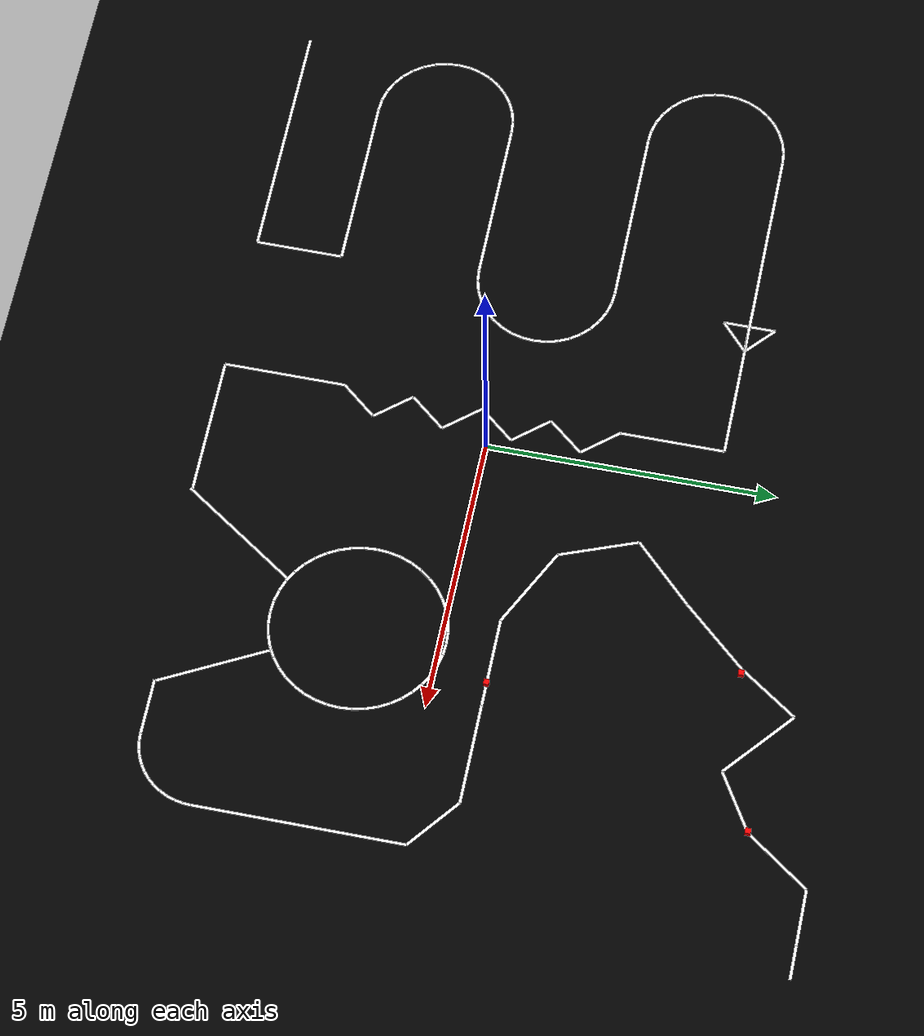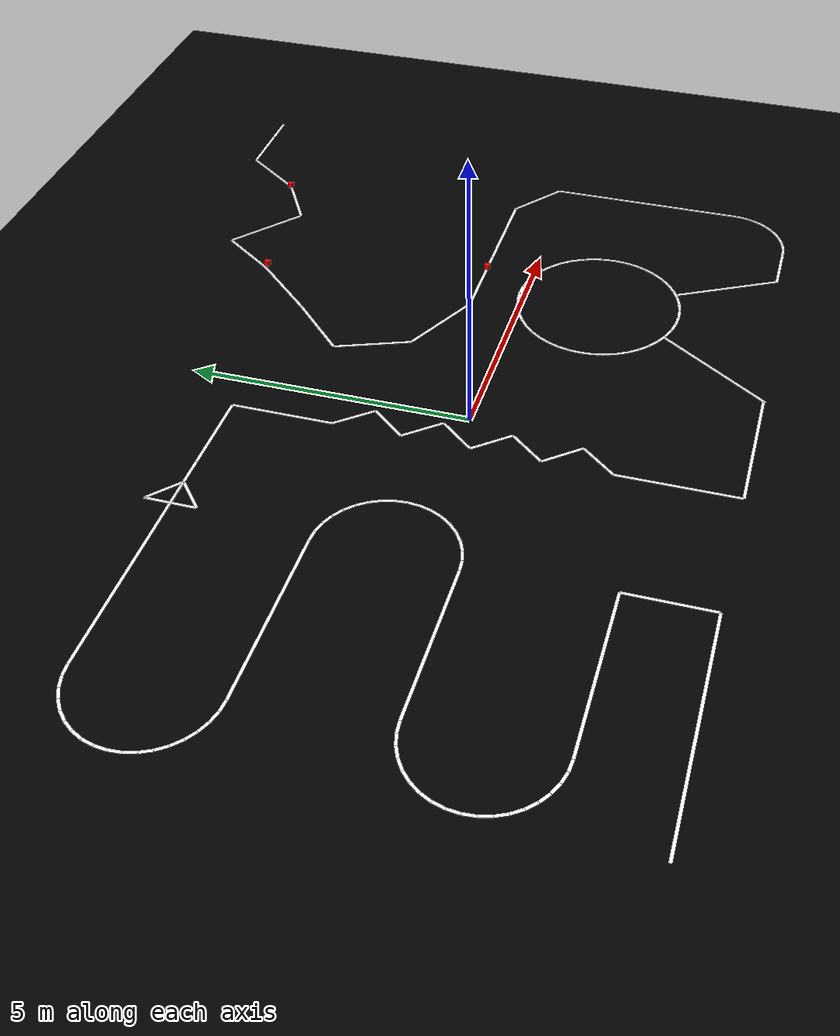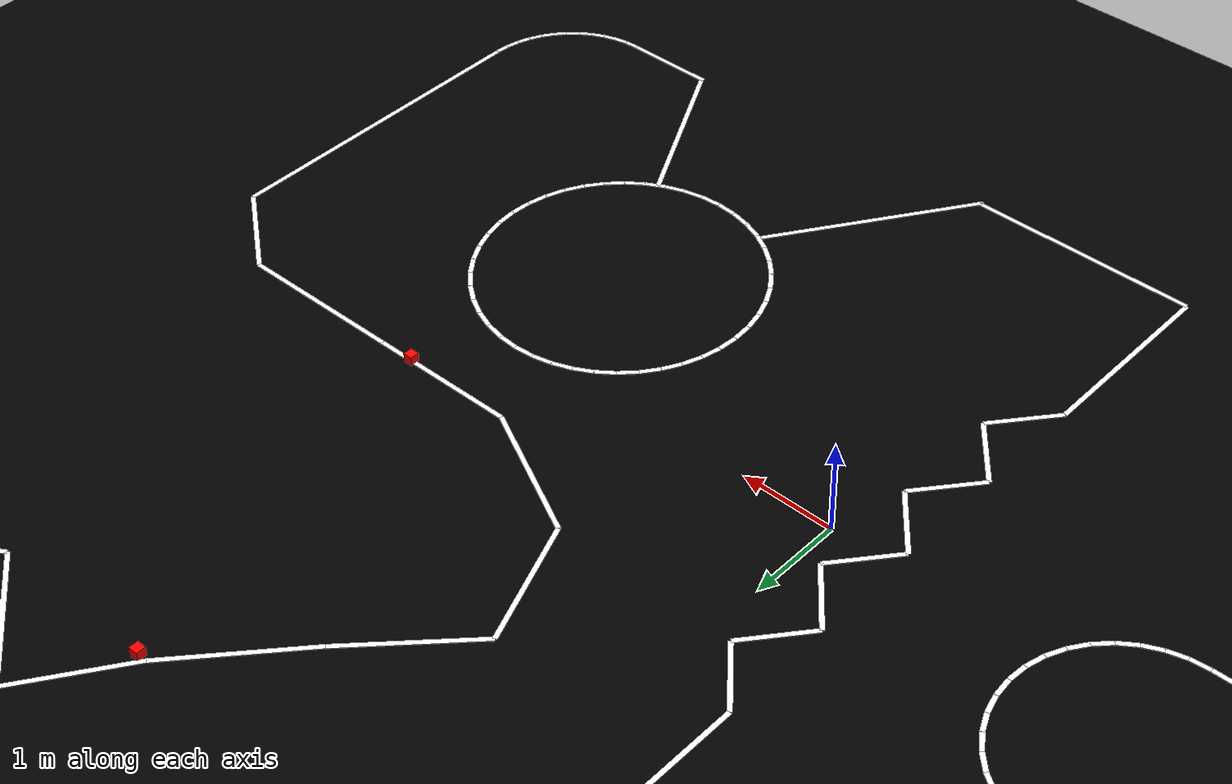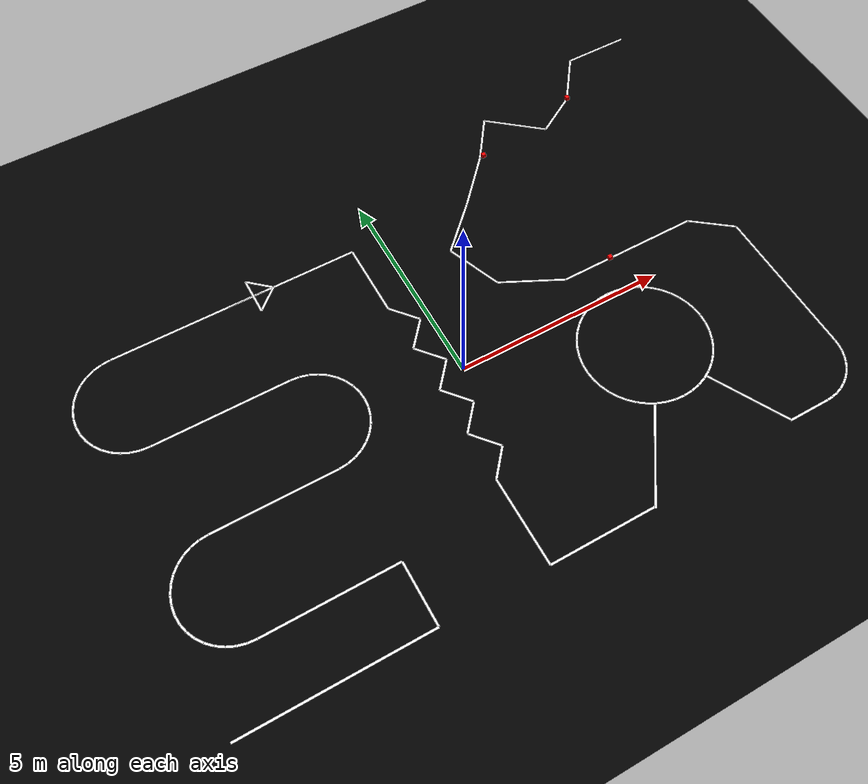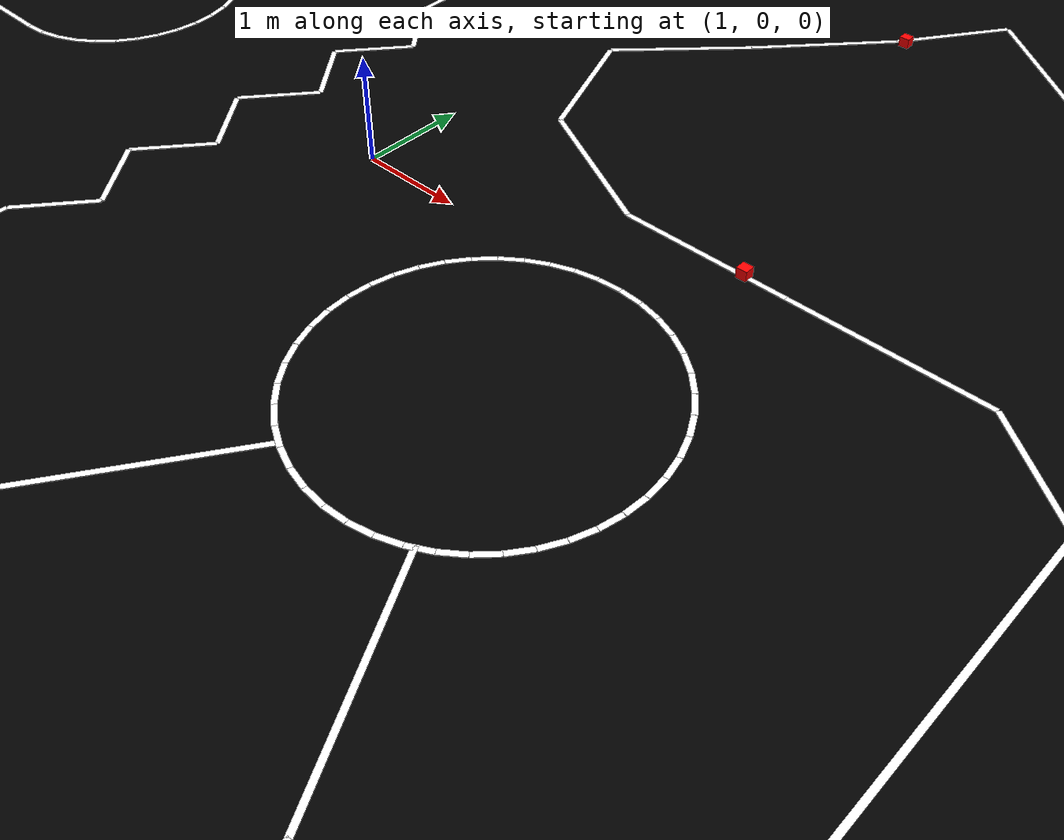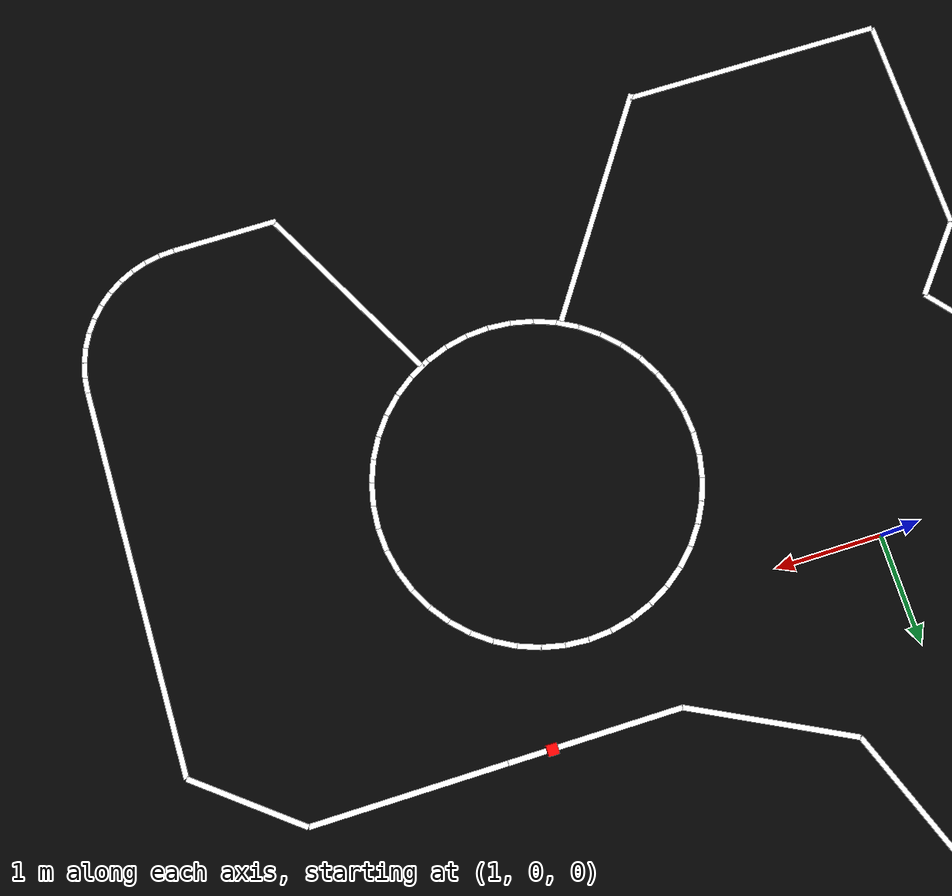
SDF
<?xml version="1.0" ?>
<sdf version="1.8">
  <world name="line_following_obstacle_world_v2">

    <plugin filename="gz-sim-physics-system" name="gz::sim::systems::Physics"/>
    <plugin filename="gz-sim-user-commands-system" name="gz::sim::systems::UserCommands"/>
    <plugin filename="gz-sim-scene-broadcaster-system" name="gz::sim::systems::SceneBroadcaster"/>

    <plugin filename="gz-sim-sensors-system" name="gz::sim::systems::Sensors">
      <render_engine>ogre2</render_engine>
    </plugin>

    <light type="directional" name="sun">
      <pose>0 0 10 0 0 0</pose>
      <diffuse>0.8 0.8 0.8 1</diffuse>
      <direction>-0.5 0.1 -0.9</direction>
    </light>

    <!-- BLACK GROUND -->
    <model name="ground_plane">
      <static>true</static>
      <link name="link">
        <collision name="collision">
          <geometry>
            <plane>
              <normal>0 0 1</normal>
              <size>25 25</size>
            </plane>
          </geometry>
        </collision>
        <visual name="visual">
          <geometry>
            <plane>
              <normal>0 0 1</normal>
              <size>25 25</size>
            </plane>
          </geometry>
          <material>
            <ambient>0 0 0 1</ambient>
            <diffuse>0 0 0 1</diffuse>
          </material>
        </visual>
      </link>
    </model>

    <!-- TRACK: white line, width = 0.05 m, thickness = 0.005 m -->
    <model name="left_top_straight">
      <static>true</static>
      <pose>-4.4000 4.0000 0.0060 0 0 0.000000</pose>
      <link name="link">
        <collision name="collision">
          <geometry>
            <box>
              <size>4.4000 0.0500 0.0050</size>
            </box>
          </geometry>
        </collision>
        <visual name="visual">
          <geometry>
            <box>
              <size>4.4000 0.0500 0.0050</size>
            </box>
          </geometry>
          <material>
            <ambient>1 1 1 1</ambient>
            <diffuse>1 1 1 1</diffuse>
          </material>
        </visual>
      </link>
    </model>
    <model name="left_top_u_1">
      <static>true</static>
      <pose>-6.7042 3.9909 0.0060 0 0 -3.054326</pose>
      <link name="link">
        <collision name="collision">
          <geometry>
            <box>
              <size>0.2092 0.0500 0.0050</size>
            </box>
          </geometry>
        </collision>
        <visual name="visual">
          <geometry>
            <box>
              <size>0.2092 0.0500 0.0050</size>
            </box>
          </geometry>
          <material>
            <ambient>1 1 1 1</ambient>
            <diffuse>1 1 1 1</diffuse>
          </material>
        </visual>
      </link>
    </model>
    <model name="left_top_u_2">
      <static>true</static>
      <pose>-6.9094 3.9547 0.0060 0 0 -2.879793</pose>
      <link name="link">
        <collision name="collision">
          <geometry>
            <box>
              <size>0.2092 0.0500 0.0050</size>
            </box>
          </geometry>
        </collision>
        <visual name="visual">
          <geometry>
            <box>
              <size>0.2092 0.0500 0.0050</size>
            </box>
          </geometry>
          <material>
            <ambient>1 1 1 1</ambient>
            <diffuse>1 1 1 1</diffuse>
          </material>
        </visual>
      </link>
    </model>
    <model name="left_top_u_3">
      <static>true</static>
      <pose>-7.1052 3.8834 0.0060 0 0 -2.705260</pose>
      <link name="link">
        <collision name="collision">
          <geometry>
            <box>
              <size>0.2092 0.0500 0.0050</size>
            </box>
          </geometry>
        </collision>
        <visual name="visual">
          <geometry>
            <box>
              <size>0.2092 0.0500 0.0050</size>
            </box>
          </geometry>
          <material>
            <ambient>1 1 1 1</ambient>
            <diffuse>1 1 1 1</diffuse>
          </material>
        </visual>
      </link>
    </model>
    <model name="left_top_u_4">
      <static>true</static>
      <pose>-7.2857 3.7792 0.0060 0 0 -2.530727</pose>
      <link name="link">
        <collision name="collision">
          <geometry>
            <box>
              <size>0.2092 0.0500 0.0050</size>
            </box>
          </geometry>
        </collision>
        <visual name="visual">
          <geometry>
            <box>
              <size>0.2092 0.0500 0.0050</size>
            </box>
          </geometry>
          <material>
            <ambient>1 1 1 1</ambient>
            <diffuse>1 1 1 1</diffuse>
          </material>
        </visual>
      </link>
    </model>
    <model name="left_top_u_5">
      <static>true</static>
      <pose>-7.4453 3.6453 0.0060 0 0 -2.356194</pose>
      <link name="link">
        <collision name="collision">
          <geometry>
            <box>
              <size>0.2092 0.0500 0.0050</size>
            </box>
          </geometry>
        </collision>
        <visual name="visual">
          <geometry>
            <box>
              <size>0.2092 0.0500 0.0050</size>
            </box>
          </geometry>
          <material>
            <ambient>1 1 1 1</ambient>
            <diffuse>1 1 1 1</diffuse>
          </material>
        </visual>
      </link>
    </model>
    <model name="left_top_u_6">
      <static>true</static>
      <pose>-7.5792 3.4857 0.0060 0 0 -2.181662</pose>
      <link name="link">
        <collision name="collision">
          <geometry>
            <box>
              <size>0.2092 0.0500 0.0050</size>
            </box>
          </geometry>
        </collision>
        <visual name="visual">
          <geometry>
            <box>
              <size>0.2092 0.0500 0.0050</size>
            </box>
          </geometry>
          <material>
            <ambient>1 1 1 1</ambient>
            <diffuse>1 1 1 1</diffuse>
          </material>
        </visual>
      </link>
    </model>
    <model name="left_top_u_7">
      <static>true</static>
      <pose>-7.6834 3.3052 0.0060 0 0 -2.007129</pose>
      <link name="link">
        <collision name="collision">
          <geometry>
            <box>
              <size>0.2092 0.0500 0.0050</size>
            </box>
          </geometry>
        </collision>
        <visual name="visual">
          <geometry>
            <box>
              <size>0.2092 0.0500 0.0050</size>
            </box>
          </geometry>
          <material>
            <ambient>1 1 1 1</ambient>
            <diffuse>1 1 1 1</diffuse>
          </material>
        </visual>
      </link>
    </model>
    <model name="left_top_u_8">
      <static>true</static>
      <pose>-7.7547 3.1094 0.0060 0 0 -1.832596</pose>
      <link name="link">
        <collision name="collision">
          <geometry>
            <box>
              <size>0.2092 0.0500 0.0050</size>
            </box>
          </geometry>
        </collision>
        <visual name="visual">
          <geometry>
            <box>
              <size>0.2092 0.0500 0.0050</size>
            </box>
          </geometry>
          <material>
            <ambient>1 1 1 1</ambient>
            <diffuse>1 1 1 1</diffuse>
          </material>
        </visual>
      </link>
    </model>
    <model name="left_top_u_9">
      <static>true</static>
      <pose>-7.7909 2.9042 0.0060 0 0 -1.658063</pose>
      <link name="link">
        <collision name="collision">
          <geometry>
            <box>
              <size>0.2092 0.0500 0.0050</size>
            </box>
          </geometry>
        </collision>
        <visual name="visual">
          <geometry>
            <box>
              <size>0.2092 0.0500 0.0050</size>
            </box>
          </geometry>
          <material>
            <ambient>1 1 1 1</ambient>
            <diffuse>1 1 1 1</diffuse>
          </material>
        </visual>
      </link>
    </model>
    <model name="left_top_u_10">
      <static>true</static>
      <pose>-7.7909 2.6958 0.0060 0 0 -1.483530</pose>
      <link name="link">
        <collision name="collision">
          <geometry>
            <box>
              <size>0.2092 0.0500 0.0050</size>
            </box>
          </geometry>
        </collision>
        <visual name="visual">
          <geometry>
            <box>
              <size>0.2092 0.0500 0.0050</size>
            </box>
          </geometry>
          <material>
            <ambient>1 1 1 1</ambient>
            <diffuse>1 1 1 1</diffuse>
          </material>
        </visual>
      </link>
    </model>
    <model name="left_top_u_11">
      <static>true</static>
      <pose>-7.7547 2.4906 0.0060 0 0 -1.308997</pose>
      <link name="link">
        <collision name="collision">
          <geometry>
            <box>
              <size>0.2092 0.0500 0.0050</size>
            </box>
          </geometry>
        </collision>
        <visual name="visual">
          <geometry>
            <box>
              <size>0.2092 0.0500 0.0050</size>
            </box>
          </geometry>
          <material>
            <ambient>1 1 1 1</ambient>
            <diffuse>1 1 1 1</diffuse>
          </material>
        </visual>
      </link>
    </model>
    <model name="left_top_u_12">
      <static>true</static>
      <pose>-7.6834 2.2948 0.0060 0 0 -1.134464</pose>
      <link name="link">
        <collision name="collision">
          <geometry>
            <box>
              <size>0.2092 0.0500 0.0050</size>
            </box>
          </geometry>
        </collision>
        <visual name="visual">
          <geometry>
            <box>
              <size>0.2092 0.0500 0.0050</size>
            </box>
          </geometry>
          <material>
            <ambient>1 1 1 1</ambient>
            <diffuse>1 1 1 1</diffuse>
          </material>
        </visual>
      </link>
    </model>
    <model name="left_top_u_13">
      <static>true</static>
      <pose>-7.5792 2.1143 0.0060 0 0 -0.959931</pose>
      <link name="link">
        <collision name="collision">
          <geometry>
            <box>
              <size>0.2092 0.0500 0.0050</size>
            </box>
          </geometry>
        </collision>
        <visual name="visual">
          <geometry>
            <box>
              <size>0.2092 0.0500 0.0050</size>
            </box>
          </geometry>
          <material>
            <ambient>1 1 1 1</ambient>
            <diffuse>1 1 1 1</diffuse>
          </material>
        </visual>
      </link>
    </model>
    <model name="left_top_u_14">
      <static>true</static>
      <pose>-7.4453 1.9547 0.0060 0 0 -0.785398</pose>
      <link name="link">
        <collision name="collision">
          <geometry>
            <box>
              <size>0.2092 0.0500 0.0050</size>
            </box>
          </geometry>
        </collision>
        <visual name="visual">
          <geometry>
            <box>
              <size>0.2092 0.0500 0.0050</size>
            </box>
          </geometry>
          <material>
            <ambient>1 1 1 1</ambient>
            <diffuse>1 1 1 1</diffuse>
          </material>
        </visual>
      </link>
    </model>
    <model name="left_top_u_15">
      <static>true</static>
      <pose>-7.2857 1.8208 0.0060 0 0 -0.610865</pose>
      <link name="link">
        <collision name="collision">
          <geometry>
            <box>
              <size>0.2092 0.0500 0.0050</size>
            </box>
          </geometry>
        </collision>
        <visual name="visual">
          <geometry>
            <box>
              <size>0.2092 0.0500 0.0050</size>
            </box>
          </geometry>
          <material>
            <ambient>1 1 1 1</ambient>
            <diffuse>1 1 1 1</diffuse>
          </material>
        </visual>
      </link>
    </model>
    <model name="left_top_u_16">
      <static>true</static>
      <pose>-7.1052 1.7166 0.0060 0 0 -0.436332</pose>
      <link name="link">
        <collision name="collision">
          <geometry>
            <box>
              <size>0.2092 0.0500 0.0050</size>
            </box>
          </geometry>
        </collision>
        <visual name="visual">
          <geometry>
            <box>
              <size>0.2092 0.0500 0.0050</size>
            </box>
          </geometry>
          <material>
            <ambient>1 1 1 1</ambient>
            <diffuse>1 1 1 1</diffuse>
          </material>
        </visual>
      </link>
    </model>
    <model name="left_top_u_17">
      <static>true</static>
      <pose>-6.9094 1.6453 0.0060 0 0 -0.261799</pose>
      <link name="link">
        <collision name="collision">
          <geometry>
            <box>
              <size>0.2092 0.0500 0.0050</size>
            </box>
          </geometry>
        </collision>
        <visual name="visual">
          <geometry>
            <box>
              <size>0.2092 0.0500 0.0050</size>
            </box>
          </geometry>
          <material>
            <ambient>1 1 1 1</ambient>
            <diffuse>1 1 1 1</diffuse>
          </material>
        </visual>
      </link>
    </model>
    <model name="left_top_u_18">
      <static>true</static>
      <pose>-6.7042 1.6091 0.0060 0 0 -0.087266</pose>
      <link name="link">
        <collision name="collision">
          <geometry>
            <box>
              <size>0.2092 0.0500 0.0050</size>
            </box>
          </geometry>
        </collision>
        <visual name="visual">
          <geometry>
            <box>
              <size>0.2092 0.0500 0.0050</size>
            </box>
          </geometry>
          <material>
            <ambient>1 1 1 1</ambient>
            <diffuse>1 1 1 1</diffuse>
          </material>
        </visual>
      </link>
    </model>
    <model name="left_mid_upper">
      <static>true</static>
      <pose>-5.0000 1.6000 0.0060 0 0 0.000000</pose>
      <link name="link">
        <collision name="collision">
          <geometry>
            <box>
              <size>3.2000 0.0500 0.0050</size>
            </box>
          </geometry>
        </collision>
        <visual name="visual">
          <geometry>
            <box>
              <size>3.2000 0.0500 0.0050</size>
            </box>
          </geometry>
          <material>
            <ambient>1 1 1 1</ambient>
            <diffuse>1 1 1 1</diffuse>
          </material>
        </visual>
      </link>
    </model>
    <model name="left_middle_right_curve_1">
      <static>true</static>
      <pose>-3.2958 1.5909 0.0060 0 0 -0.087266</pose>
      <link name="link">
        <collision name="collision">
          <geometry>
            <box>
              <size>0.2092 0.0500 0.0050</size>
            </box>
          </geometry>
        </collision>
        <visual name="visual">
          <geometry>
            <box>
              <size>0.2092 0.0500 0.0050</size>
            </box>
          </geometry>
          <material>
            <ambient>1 1 1 1</ambient>
            <diffuse>1 1 1 1</diffuse>
          </material>
        </visual>
      </link>
    </model>
    <model name="left_middle_right_curve_2">
      <static>true</static>
      <pose>-3.0906 1.5547 0.0060 0 0 -0.261799</pose>
      <link name="link">
        <collision name="collision">
          <geometry>
            <box>
              <size>0.2092 0.0500 0.0050</size>
            </box>
          </geometry>
        </collision>
        <visual name="visual">
          <geometry>
            <box>
              <size>0.2092 0.0500 0.0050</size>
            </box>
          </geometry>
          <material>
            <ambient>1 1 1 1</ambient>
            <diffuse>1 1 1 1</diffuse>
          </material>
        </visual>
      </link>
    </model>
    <model name="left_middle_right_curve_3">
      <static>true</static>
      <pose>-2.8948 1.4834 0.0060 0 0 -0.436332</pose>
      <link name="link">
        <collision name="collision">
          <geometry>
            <box>
              <size>0.2092 0.0500 0.0050</size>
            </box>
          </geometry>
        </collision>
        <visual name="visual">
          <geometry>
            <box>
              <size>0.2092 0.0500 0.0050</size>
            </box>
          </geometry>
          <material>
            <ambient>1 1 1 1</ambient>
            <diffuse>1 1 1 1</diffuse>
          </material>
        </visual>
      </link>
    </model>
    <model name="left_middle_right_curve_4">
      <static>true</static>
      <pose>-2.7143 1.3792 0.0060 0 0 -0.610865</pose>
      <link name="link">
        <collision name="collision">
          <geometry>
            <box>
              <size>0.2092 0.0500 0.0050</size>
            </box>
          </geometry>
        </collision>
        <visual name="visual">
          <geometry>
            <box>
              <size>0.2092 0.0500 0.0050</size>
            </box>
          </geometry>
          <material>
            <ambient>1 1 1 1</ambient>
            <diffuse>1 1 1 1</diffuse>
          </material>
        </visual>
      </link>
    </model>
    <model name="left_middle_right_curve_5">
      <static>true</static>
      <pose>-2.5547 1.2453 0.0060 0 0 -0.785398</pose>
      <link name="link">
        <collision name="collision">
          <geometry>
            <box>
              <size>0.2092 0.0500 0.0050</size>
            </box>
          </geometry>
        </collision>
        <visual name="visual">
          <geometry>
            <box>
              <size>0.2092 0.0500 0.0050</size>
            </box>
          </geometry>
          <material>
            <ambient>1 1 1 1</ambient>
            <diffuse>1 1 1 1</diffuse>
          </material>
        </visual>
      </link>
    </model>
    <model name="left_middle_right_curve_6">
      <static>true</static>
      <pose>-2.4208 1.0857 0.0060 0 0 -0.959931</pose>
      <link name="link">
        <collision name="collision">
          <geometry>
            <box>
              <size>0.2092 0.0500 0.0050</size>
            </box>
          </geometry>
        </collision>
        <visual name="visual">
          <geometry>
            <box>
              <size>0.2092 0.0500 0.0050</size>
            </box>
          </geometry>
          <material>
            <ambient>1 1 1 1</ambient>
            <diffuse>1 1 1 1</diffuse>
          </material>
        </visual>
      </link>
    </model>
    <model name="left_middle_right_curve_7">
      <static>true</static>
      <pose>-2.3166 0.9052 0.0060 0 0 -1.134464</pose>
      <link name="link">
        <collision name="collision">
          <geometry>
            <box>
              <size>0.2092 0.0500 0.0050</size>
            </box>
          </geometry>
        </collision>
        <visual name="visual">
          <geometry>
            <box>
              <size>0.2092 0.0500 0.0050</size>
            </box>
          </geometry>
          <material>
            <ambient>1 1 1 1</ambient>
            <diffuse>1 1 1 1</diffuse>
          </material>
        </visual>
      </link>
    </model>
    <model name="left_middle_right_curve_8">
      <static>true</static>
      <pose>-2.2453 0.7094 0.0060 0 0 -1.308997</pose>
      <link name="link">
        <collision name="collision">
          <geometry>
            <box>
              <size>0.2092 0.0500 0.0050</size>
            </box>
          </geometry>
        </collision>
        <visual name="visual">
          <geometry>
            <box>
              <size>0.2092 0.0500 0.0050</size>
            </box>
          </geometry>
          <material>
            <ambient>1 1 1 1</ambient>
            <diffuse>1 1 1 1</diffuse>
          </material>
        </visual>
      </link>
    </model>
    <model name="left_middle_right_curve_9">
      <static>true</static>
      <pose>-2.2091 0.5042 0.0060 0 0 -1.483530</pose>
      <link name="link">
        <collision name="collision">
          <geometry>
            <box>
              <size>0.2092 0.0500 0.0050</size>
            </box>
          </geometry>
        </collision>
        <visual name="visual">
          <geometry>
            <box>
              <size>0.2092 0.0500 0.0050</size>
            </box>
          </geometry>
          <material>
            <ambient>1 1 1 1</ambient>
            <diffuse>1 1 1 1</diffuse>
          </material>
        </visual>
      </link>
    </model>
    <model name="left_middle_right_curve_10">
      <static>true</static>
      <pose>-2.2091 0.2958 0.0060 0 0 -1.658063</pose>
      <link name="link">
        <collision name="collision">
          <geometry>
            <box>
              <size>0.2092 0.0500 0.0050</size>
            </box>
          </geometry>
        </collision>
        <visual name="visual">
          <geometry>
            <box>
              <size>0.2092 0.0500 0.0050</size>
            </box>
          </geometry>
          <material>
            <ambient>1 1 1 1</ambient>
            <diffuse>1 1 1 1</diffuse>
          </material>
        </visual>
      </link>
    </model>
    <model name="left_middle_right_curve_11">
      <static>true</static>
      <pose>-2.2453 0.0906 0.0060 0 0 -1.832596</pose>
      <link name="link">
        <collision name="collision">
          <geometry>
            <box>
              <size>0.2092 0.0500 0.0050</size>
            </box>
          </geometry>
        </collision>
        <visual name="visual">
          <geometry>
            <box>
              <size>0.2092 0.0500 0.0050</size>
            </box>
          </geometry>
          <material>
            <ambient>1 1 1 1</ambient>
            <diffuse>1 1 1 1</diffuse>
          </material>
        </visual>
      </link>
    </model>
    <model name="left_middle_right_curve_12">
      <static>true</static>
      <pose>-2.3166 -0.1052 0.0060 0 0 -2.007129</pose>
      <link name="link">
        <collision name="collision">
          <geometry>
            <box>
              <size>0.2092 0.0500 0.0050</size>
            </box>
          </geometry>
        </collision>
        <visual name="visual">
          <geometry>
            <box>
              <size>0.2092 0.0500 0.0050</size>
            </box>
          </geometry>
          <material>
            <ambient>1 1 1 1</ambient>
            <diffuse>1 1 1 1</diffuse>
          </material>
        </visual>
      </link>
    </model>
    <model name="left_middle_right_curve_13">
      <static>true</static>
      <pose>-2.4208 -0.2857 0.0060 0 0 -2.181662</pose>
      <link name="link">
        <collision name="collision">
          <geometry>
            <box>
              <size>0.2092 0.0500 0.0050</size>
            </box>
          </geometry>
        </collision>
        <visual name="visual">
          <geometry>
            <box>
              <size>0.2092 0.0500 0.0050</size>
            </box>
          </geometry>
          <material>
            <ambient>1 1 1 1</ambient>
            <diffuse>1 1 1 1</diffuse>
          </material>
        </visual>
      </link>
    </model>
    <model name="left_middle_right_curve_14">
      <static>true</static>
      <pose>-2.5547 -0.4453 0.0060 0 0 -2.356194</pose>
      <link name="link">
        <collision name="collision">
          <geometry>
            <box>
              <size>0.2092 0.0500 0.0050</size>
            </box>
          </geometry>
        </collision>
        <visual name="visual">
          <geometry>
            <box>
              <size>0.2092 0.0500 0.0050</size>
            </box>
          </geometry>
          <material>
            <ambient>1 1 1 1</ambient>
            <diffuse>1 1 1 1</diffuse>
          </material>
        </visual>
      </link>
    </model>
    <model name="left_middle_right_curve_15">
      <static>true</static>
      <pose>-2.7143 -0.5792 0.0060 0 0 -2.530727</pose>
      <link name="link">
        <collision name="collision">
          <geometry>
            <box>
              <size>0.2092 0.0500 0.0050</size>
            </box>
          </geometry>
        </collision>
        <visual name="visual">
          <geometry>
            <box>
              <size>0.2092 0.0500 0.0050</size>
            </box>
          </geometry>
          <material>
            <ambient>1 1 1 1</ambient>
            <diffuse>1 1 1 1</diffuse>
          </material>
        </visual>
      </link>
    </model>
    <model name="left_middle_right_curve_16">
      <static>true</static>
      <pose>-2.8948 -0.6834 0.0060 0 0 -2.705260</pose>
      <link name="link">
        <collision name="collision">
          <geometry>
            <box>
              <size>0.2092 0.0500 0.0050</size>
            </box>
          </geometry>
        </collision>
        <visual name="visual">
          <geometry>
            <box>
              <size>0.2092 0.0500 0.0050</size>
            </box>
          </geometry>
          <material>
            <ambient>1 1 1 1</ambient>
            <diffuse>1 1 1 1</diffuse>
          </material>
        </visual>
      </link>
    </model>
    <model name="left_middle_right_curve_17">
      <static>true</static>
      <pose>-3.0906 -0.7547 0.0060 0 0 -2.879793</pose>
      <link name="link">
        <collision name="collision">
          <geometry>
            <box>
              <size>0.2092 0.0500 0.0050</size>
            </box>
          </geometry>
        </collision>
        <visual name="visual">
          <geometry>
            <box>
              <size>0.2092 0.0500 0.0050</size>
            </box>
          </geometry>
          <material>
            <ambient>1 1 1 1</ambient>
            <diffuse>1 1 1 1</diffuse>
          </material>
        </visual>
      </link>
    </model>
    <model name="left_middle_right_curve_18">
      <static>true</static>
      <pose>-3.2958 -0.7909 0.0060 0 0 -3.054326</pose>
      <link name="link">
        <collision name="collision">
          <geometry>
            <box>
              <size>0.2092 0.0500 0.0050</size>
            </box>
          </geometry>
        </collision>
        <visual name="visual">
          <geometry>
            <box>
              <size>0.2092 0.0500 0.0050</size>
            </box>
          </geometry>
          <material>
            <ambient>1 1 1 1</ambient>
            <diffuse>1 1 1 1</diffuse>
          </material>
        </visual>
      </link>
    </model>
    <model name="left_mid_lower">
      <static>true</static>
      <pose>-4.8500 -0.8000 0.0060 0 0 3.141593</pose>
      <link name="link">
        <collision name="collision">
          <geometry>
            <box>
              <size>2.9000 0.0500 0.0050</size>
            </box>
          </geometry>
        </collision>
        <visual name="visual">
          <geometry>
            <box>
              <size>2.9000 0.0500 0.0050</size>
            </box>
          </geometry>
          <material>
            <ambient>1 1 1 1</ambient>
            <diffuse>1 1 1 1</diffuse>
          </material>
        </visual>
      </link>
    </model>
    <model name="left_bottom_u_1">
      <static>true</static>
      <pose>-6.4042 -0.8091 0.0060 0 0 -3.054326</pose>
      <link name="link">
        <collision name="collision">
          <geometry>
            <box>
              <size>0.2092 0.0500 0.0050</size>
            </box>
          </geometry>
        </collision>
        <visual name="visual">
          <geometry>
            <box>
              <size>0.2092 0.0500 0.0050</size>
            </box>
          </geometry>
          <material>
            <ambient>1 1 1 1</ambient>
            <diffuse>1 1 1 1</diffuse>
          </material>
        </visual>
      </link>
    </model>
    <model name="left_bottom_u_2">
      <static>true</static>
      <pose>-6.6094 -0.8453 0.0060 0 0 -2.879793</pose>
      <link name="link">
        <collision name="collision">
          <geometry>
            <box>
              <size>0.2092 0.0500 0.0050</size>
            </box>
          </geometry>
        </collision>
        <visual name="visual">
          <geometry>
            <box>
              <size>0.2092 0.0500 0.0050</size>
            </box>
          </geometry>
          <material>
            <ambient>1 1 1 1</ambient>
            <diffuse>1 1 1 1</diffuse>
          </material>
        </visual>
      </link>
    </model>
    <model name="left_bottom_u_3">
      <static>true</static>
      <pose>-6.8052 -0.9166 0.0060 0 0 -2.705260</pose>
      <link name="link">
        <collision name="collision">
          <geometry>
            <box>
              <size>0.2092 0.0500 0.0050</size>
            </box>
          </geometry>
        </collision>
        <visual name="visual">
          <geometry>
            <box>
              <size>0.2092 0.0500 0.0050</size>
            </box>
          </geometry>
          <material>
            <ambient>1 1 1 1</ambient>
            <diffuse>1 1 1 1</diffuse>
          </material>
        </visual>
      </link>
    </model>
    <model name="left_bottom_u_4">
      <static>true</static>
      <pose>-6.9857 -1.0208 0.0060 0 0 -2.530727</pose>
      <link name="link">
        <collision name="collision">
          <geometry>
            <box>
              <size>0.2092 0.0500 0.0050</size>
            </box>
          </geometry>
        </collision>
        <visual name="visual">
          <geometry>
            <box>
              <size>0.2092 0.0500 0.0050</size>
            </box>
          </geometry>
          <material>
            <ambient>1 1 1 1</ambient>
            <diffuse>1 1 1 1</diffuse>
          </material>
        </visual>
      </link>
    </model>
    <model name="left_bottom_u_5">
      <static>true</static>
      <pose>-7.1453 -1.1547 0.0060 0 0 -2.356194</pose>
      <link name="link">
        <collision name="collision">
          <geometry>
            <box>
              <size>0.2092 0.0500 0.0050</size>
            </box>
          </geometry>
        </collision>
        <visual name="visual">
          <geometry>
            <box>
              <size>0.2092 0.0500 0.0050</size>
            </box>
          </geometry>
          <material>
            <ambient>1 1 1 1</ambient>
            <diffuse>1 1 1 1</diffuse>
          </material>
        </visual>
      </link>
    </model>
    <model name="left_bottom_u_6">
      <static>true</static>
      <pose>-7.2792 -1.3143 0.0060 0 0 -2.181662</pose>
      <link name="link">
        <collision name="collision">
          <geometry>
            <box>
              <size>0.2092 0.0500 0.0050</size>
            </box>
          </geometry>
        </collision>
        <visual name="visual">
          <geometry>
            <box>
              <size>0.2092 0.0500 0.0050</size>
            </box>
          </geometry>
          <material>
            <ambient>1 1 1 1</ambient>
            <diffuse>1 1 1 1</diffuse>
          </material>
        </visual>
      </link>
    </model>
    <model name="left_bottom_u_7">
      <static>true</static>
      <pose>-7.3834 -1.4948 0.0060 0 0 -2.007129</pose>
      <link name="link">
        <collision name="collision">
          <geometry>
            <box>
              <size>0.2092 0.0500 0.0050</size>
            </box>
          </geometry>
        </collision>
        <visual name="visual">
          <geometry>
            <box>
              <size>0.2092 0.0500 0.0050</size>
            </box>
          </geometry>
          <material>
            <ambient>1 1 1 1</ambient>
            <diffuse>1 1 1 1</diffuse>
          </material>
        </visual>
      </link>
    </model>
    <model name="left_bottom_u_8">
      <static>true</static>
      <pose>-7.4547 -1.6906 0.0060 0 0 -1.832596</pose>
      <link name="link">
        <collision name="collision">
          <geometry>
            <box>
              <size>0.2092 0.0500 0.0050</size>
            </box>
          </geometry>
        </collision>
        <visual name="visual">
          <geometry>
            <box>
              <size>0.2092 0.0500 0.0050</size>
            </box>
          </geometry>
          <material>
            <ambient>1 1 1 1</ambient>
            <diffuse>1 1 1 1</diffuse>
          </material>
        </visual>
      </link>
    </model>
    <model name="left_bottom_u_9">
      <static>true</static>
      <pose>-7.4909 -1.8958 0.0060 0 0 -1.658063</pose>
      <link name="link">
        <collision name="collision">
          <geometry>
            <box>
              <size>0.2092 0.0500 0.0050</size>
            </box>
          </geometry>
        </collision>
        <visual name="visual">
          <geometry>
            <box>
              <size>0.2092 0.0500 0.0050</size>
            </box>
          </geometry>
          <material>
            <ambient>1 1 1 1</ambient>
            <diffuse>1 1 1 1</diffuse>
          </material>
        </visual>
      </link>
    </model>
    <model name="left_bottom_u_10">
      <static>true</static>
      <pose>-7.4909 -2.1042 0.0060 0 0 -1.483530</pose>
      <link name="link">
        <collision name="collision">
          <geometry>
            <box>
              <size>0.2092 0.0500 0.0050</size>
            </box>
          </geometry>
        </collision>
        <visual name="visual">
          <geometry>
            <box>
              <size>0.2092 0.0500 0.0050</size>
            </box>
          </geometry>
          <material>
            <ambient>1 1 1 1</ambient>
            <diffuse>1 1 1 1</diffuse>
          </material>
        </visual>
      </link>
    </model>
    <model name="left_bottom_u_11">
      <static>true</static>
      <pose>-7.4547 -2.3094 0.0060 0 0 -1.308997</pose>
      <link name="link">
        <collision name="collision">
          <geometry>
            <box>
              <size>0.2092 0.0500 0.0050</size>
            </box>
          </geometry>
        </collision>
        <visual name="visual">
          <geometry>
            <box>
              <size>0.2092 0.0500 0.0050</size>
            </box>
          </geometry>
          <material>
            <ambient>1 1 1 1</ambient>
            <diffuse>1 1 1 1</diffuse>
          </material>
        </visual>
      </link>
    </model>
    <model name="left_bottom_u_12">
      <static>true</static>
      <pose>-7.3834 -2.5052 0.0060 0 0 -1.134464</pose>
      <link name="link">
        <collision name="collision">
          <geometry>
            <box>
              <size>0.2092 0.0500 0.0050</size>
            </box>
          </geometry>
        </collision>
        <visual name="visual">
          <geometry>
            <box>
              <size>0.2092 0.0500 0.0050</size>
            </box>
          </geometry>
          <material>
            <ambient>1 1 1 1</ambient>
            <diffuse>1 1 1 1</diffuse>
          </material>
        </visual>
      </link>
    </model>
    <model name="left_bottom_u_13">
      <static>true</static>
      <pose>-7.2792 -2.6857 0.0060 0 0 -0.959931</pose>
      <link name="link">
        <collision name="collision">
          <geometry>
            <box>
              <size>0.2092 0.0500 0.0050</size>
            </box>
          </geometry>
        </collision>
        <visual name="visual">
          <geometry>
            <box>
              <size>0.2092 0.0500 0.0050</size>
            </box>
          </geometry>
          <material>
            <ambient>1 1 1 1</ambient>
            <diffuse>1 1 1 1</diffuse>
          </material>
        </visual>
      </link>
    </model>
    <model name="left_bottom_u_14">
      <static>true</static>
      <pose>-7.1453 -2.8453 0.0060 0 0 -0.785398</pose>
      <link name="link">
        <collision name="collision">
          <geometry>
            <box>
              <size>0.2092 0.0500 0.0050</size>
            </box>
          </geometry>
        </collision>
        <visual name="visual">
          <geometry>
            <box>
              <size>0.2092 0.0500 0.0050</size>
            </box>
          </geometry>
          <material>
            <ambient>1 1 1 1</ambient>
            <diffuse>1 1 1 1</diffuse>
          </material>
        </visual>
      </link>
    </model>
    <model name="left_bottom_u_15">
      <static>true</static>
      <pose>-6.9857 -2.9792 0.0060 0 0 -0.610865</pose>
      <link name="link">
        <collision name="collision">
          <geometry>
            <box>
              <size>0.2092 0.0500 0.0050</size>
            </box>
          </geometry>
        </collision>
        <visual name="visual">
          <geometry>
            <box>
              <size>0.2092 0.0500 0.0050</size>
            </box>
          </geometry>
          <material>
            <ambient>1 1 1 1</ambient>
            <diffuse>1 1 1 1</diffuse>
          </material>
        </visual>
      </link>
    </model>
    <model name="left_bottom_u_16">
      <static>true</static>
      <pose>-6.8052 -3.0834 0.0060 0 0 -0.436332</pose>
      <link name="link">
        <collision name="collision">
          <geometry>
            <box>
              <size>0.2092 0.0500 0.0050</size>
            </box>
          </geometry>
        </collision>
        <visual name="visual">
          <geometry>
            <box>
              <size>0.2092 0.0500 0.0050</size>
            </box>
          </geometry>
          <material>
            <ambient>1 1 1 1</ambient>
            <diffuse>1 1 1 1</diffuse>
          </material>
        </visual>
      </link>
    </model>
    <model name="left_bottom_u_17">
      <static>true</static>
      <pose>-6.6094 -3.1547 0.0060 0 0 -0.261799</pose>
      <link name="link">
        <collision name="collision">
          <geometry>
            <box>
              <size>0.2092 0.0500 0.0050</size>
            </box>
          </geometry>
        </collision>
        <visual name="visual">
          <geometry>
            <box>
              <size>0.2092 0.0500 0.0050</size>
            </box>
          </geometry>
          <material>
            <ambient>1 1 1 1</ambient>
            <diffuse>1 1 1 1</diffuse>
          </material>
        </visual>
      </link>
    </model>
    <model name="left_bottom_u_18">
      <static>true</static>
      <pose>-6.4042 -3.1909 0.0060 0 0 -0.087266</pose>
      <link name="link">
        <collision name="collision">
          <geometry>
            <box>
              <size>0.2092 0.0500 0.0050</size>
            </box>
          </geometry>
        </collision>
        <visual name="visual">
          <geometry>
            <box>
              <size>0.2092 0.0500 0.0050</size>
            </box>
          </geometry>
          <material>
            <ambient>1 1 1 1</ambient>
            <diffuse>1 1 1 1</diffuse>
          </material>
        </visual>
      </link>
    </model>
    <model name="left_lower_straight">
      <static>true</static>
      <pose>-4.7500 -3.2000 0.0060 0 0 0.000000</pose>
      <link name="link">
        <collision name="collision">
          <geometry>
            <box>
              <size>3.1000 0.0500 0.0050</size>
            </box>
          </geometry>
        </collision>
        <visual name="visual">
          <geometry>
            <box>
              <size>3.1000 0.0500 0.0050</size>
            </box>
          </geometry>
          <material>
            <ambient>1 1 1 1</ambient>
            <diffuse>1 1 1 1</diffuse>
          </material>
        </visual>
      </link>
    </model>
    <model name="left_bottom_exit">
      <static>true</static>
      <pose>-3.2000 -3.9500 0.0060 0 0 -1.570796</pose>
      <link name="link">
        <collision name="collision">
          <geometry>
            <box>
              <size>1.5000 0.0500 0.0050</size>
            </box>
          </geometry>
        </collision>
        <visual name="visual">
          <geometry>
            <box>
              <size>1.5000 0.0500 0.0050</size>
            </box>
          </geometry>
          <material>
            <ambient>1 1 1 1</ambient>
            <diffuse>1 1 1 1</diffuse>
          </material>
        </visual>
      </link>
    </model>
    <model name="left_bottom_short">
      <static>true</static>
      <pose>-5.3500 -4.7000 0.0060 0 0 0.000000</pose>
      <link name="link">
        <collision name="collision">
          <geometry>
            <box>
              <size>4.3000 0.0500 0.0050</size>
            </box>
          </geometry>
        </collision>
        <visual name="visual">
          <geometry>
            <box>
              <size>4.3000 0.0500 0.0050</size>
            </box>
          </geometry>
          <material>
            <ambient>1 1 1 1</ambient>
            <diffuse>1 1 1 1</diffuse>
          </material>
        </visual>
      </link>
    </model>
    <model name="arrow_tail">
      <static>true</static>
      <pose>-3.2500 4.0000 0.0060 0 0 0.000000</pose>
      <link name="link">
        <collision name="collision">
          <geometry>
            <box>
              <size>1.1000 0.0500 0.0050</size>
            </box>
          </geometry>
        </collision>
        <visual name="visual">
          <geometry>
            <box>
              <size>1.1000 0.0500 0.0050</size>
            </box>
          </geometry>
          <material>
            <ambient>1 1 1 1</ambient>
            <diffuse>1 1 1 1</diffuse>
          </material>
        </visual>
      </link>
    </model>
    <model name="arrow_head_top">
      <static>true</static>
      <pose>-2.9500 4.2250 0.0060 0 0 2.408778</pose>
      <link name="link">
        <collision name="collision">
          <geometry>
            <box>
              <size>0.6727 0.0500 0.0050</size>
            </box>
          </geometry>
        </collision>
        <visual name="visual">
          <geometry>
            <box>
              <size>0.6727 0.0500 0.0050</size>
            </box>
          </geometry>
          <material>
            <ambient>1 1 1 1</ambient>
            <diffuse>1 1 1 1</diffuse>
          </material>
        </visual>
      </link>
    </model>
    <model name="arrow_head_bottom">
      <static>true</static>
      <pose>-2.9500 3.7750 0.0060 0 0 -2.408778</pose>
      <link name="link">
        <collision name="collision">
          <geometry>
            <box>
              <size>0.6727 0.0500 0.0050</size>
            </box>
          </geometry>
        </collision>
        <visual name="visual">
          <geometry>
            <box>
              <size>0.6727 0.0500 0.0050</size>
            </box>
          </geometry>
          <material>
            <ambient>1 1 1 1</ambient>
            <diffuse>1 1 1 1</diffuse>
          </material>
        </visual>
      </link>
    </model>
    <model name="arrow_head_back">
      <static>true</static>
      <pose>-3.2000 4.0000 0.0060 0 0 -1.570796</pose>
      <link name="link">
        <collision name="collision">
          <geometry>
            <box>
              <size>0.9000 0.0500 0.0050</size>
            </box>
          </geometry>
        </collision>
        <visual name="visual">
          <geometry>
            <box>
              <size>0.9000 0.0500 0.0050</size>
            </box>
          </geometry>
          <material>
            <ambient>1 1 1 1</ambient>
            <diffuse>1 1 1 1</diffuse>
          </material>
        </visual>
      </link>
    </model>
    <model name="center_vertical_top">
      <static>true</static>
      <pose>-0.7000 3.1000 0.0060 0 0 -1.570796</pose>
      <link name="link">
        <collision name="collision">
          <geometry>
            <box>
              <size>1.8000 0.0500 0.0050</size>
            </box>
          </geometry>
        </collision>
        <visual name="visual">
          <geometry>
            <box>
              <size>1.8000 0.0500 0.0050</size>
            </box>
          </geometry>
          <material>
            <ambient>1 1 1 1</ambient>
            <diffuse>1 1 1 1</diffuse>
          </material>
        </visual>
      </link>
    </model>
    <model name="center_connector">
      <static>true</static>
      <pose>-1.4500 4.0000 0.0060 0 0 0.000000</pose>
      <link name="link">
        <collision name="collision">
          <geometry>
            <box>
              <size>1.5000 0.0500 0.0050</size>
            </box>
          </geometry>
        </collision>
        <visual name="visual">
          <geometry>
            <box>
              <size>1.5000 0.0500 0.0050</size>
            </box>
          </geometry>
          <material>
            <ambient>1 1 1 1</ambient>
            <diffuse>1 1 1 1</diffuse>
          </material>
        </visual>
      </link>
    </model>
    <model name="center_zigzag_1">
      <static>true</static>
      <pose>-0.4500 1.9000 0.0060 0 0 -0.876058</pose>
      <link name="link">
        <collision name="collision">
          <geometry>
            <box>
              <size>0.7810 0.0500 0.0050</size>
            </box>
          </geometry>
        </collision>
        <visual name="visual">
          <geometry>
            <box>
              <size>0.7810 0.0500 0.0050</size>
            </box>
          </geometry>
          <material>
            <ambient>1 1 1 1</ambient>
            <diffuse>1 1 1 1</diffuse>
          </material>
        </visual>
      </link>
    </model>
    <model name="center_zigzag_2">
      <static>true</static>
      <pose>-0.4500 1.3000 0.0060 0 0 -2.265535</pose>
      <link name="link">
        <collision name="collision">
          <geometry>
            <box>
              <size>0.7810 0.0500 0.0050</size>
            </box>
          </geometry>
        </collision>
        <visual name="visual">
          <geometry>
            <box>
              <size>0.7810 0.0500 0.0050</size>
            </box>
          </geometry>
          <material>
            <ambient>1 1 1 1</ambient>
            <diffuse>1 1 1 1</diffuse>
          </material>
        </visual>
      </link>
    </model>
    <model name="center_zigzag_3">
      <static>true</static>
      <pose>-0.4500 0.7000 0.0060 0 0 -0.876058</pose>
      <link name="link">
        <collision name="collision">
          <geometry>
            <box>
              <size>0.7810 0.0500 0.0050</size>
            </box>
          </geometry>
        </collision>
        <visual name="visual">
          <geometry>
            <box>
              <size>0.7810 0.0500 0.0050</size>
            </box>
          </geometry>
          <material>
            <ambient>1 1 1 1</ambient>
            <diffuse>1 1 1 1</diffuse>
          </material>
        </visual>
      </link>
    </model>
    <model name="center_zigzag_4">
      <static>true</static>
      <pose>-0.4500 0.1000 0.0060 0 0 -2.265535</pose>
      <link name="link">
        <collision name="collision">
          <geometry>
            <box>
              <size>0.7810 0.0500 0.0050</size>
            </box>
          </geometry>
        </collision>
        <visual name="visual">
          <geometry>
            <box>
              <size>0.7810 0.0500 0.0050</size>
            </box>
          </geometry>
          <material>
            <ambient>1 1 1 1</ambient>
            <diffuse>1 1 1 1</diffuse>
          </material>
        </visual>
      </link>
    </model>
    <model name="center_zigzag_5">
      <static>true</static>
      <pose>-0.4500 -0.5000 0.0060 0 0 -0.876058</pose>
      <link name="link">
        <collision name="collision">
          <geometry>
            <box>
              <size>0.7810 0.0500 0.0050</size>
            </box>
          </geometry>
        </collision>
        <visual name="visual">
          <geometry>
            <box>
              <size>0.7810 0.0500 0.0050</size>
            </box>
          </geometry>
          <material>
            <ambient>1 1 1 1</ambient>
            <diffuse>1 1 1 1</diffuse>
          </material>
        </visual>
      </link>
    </model>
    <model name="center_zigzag_6">
      <static>true</static>
      <pose>-0.4500 -1.1000 0.0060 0 0 -2.265535</pose>
      <link name="link">
        <collision name="collision">
          <geometry>
            <box>
              <size>0.7810 0.0500 0.0050</size>
            </box>
          </geometry>
        </collision>
        <visual name="visual">
          <geometry>
            <box>
              <size>0.7810 0.0500 0.0050</size>
            </box>
          </geometry>
          <material>
            <ambient>1 1 1 1</ambient>
            <diffuse>1 1 1 1</diffuse>
          </material>
        </visual>
      </link>
    </model>
    <model name="center_zigzag_7">
      <static>true</static>
      <pose>-0.4500 -1.7000 0.0060 0 0 -0.876058</pose>
      <link name="link">
        <collision name="collision">
          <geometry>
            <box>
              <size>0.7810 0.0500 0.0050</size>
            </box>
          </geometry>
        </collision>
        <visual name="visual">
          <geometry>
            <box>
              <size>0.7810 0.0500 0.0050</size>
            </box>
          </geometry>
          <material>
            <ambient>1 1 1 1</ambient>
            <diffuse>1 1 1 1</diffuse>
          </material>
        </visual>
      </link>
    </model>
    <model name="center_zigzag_8">
      <static>true</static>
      <pose>-0.4500 -2.3000 0.0060 0 0 -2.265535</pose>
      <link name="link">
        <collision name="collision">
          <geometry>
            <box>
              <size>0.7810 0.0500 0.0050</size>
            </box>
          </geometry>
        </collision>
        <visual name="visual">
          <geometry>
            <box>
              <size>0.7810 0.0500 0.0050</size>
            </box>
          </geometry>
          <material>
            <ambient>1 1 1 1</ambient>
            <diffuse>1 1 1 1</diffuse>
          </material>
        </visual>
      </link>
    </model>
    <model name="center_zigzag_9">
      <static>true</static>
      <pose>-0.7000 -3.6500 0.0060 0 0 -1.570796</pose>
      <link name="link">
        <collision name="collision">
          <geometry>
            <box>
              <size>2.1000 0.0500 0.0050</size>
            </box>
          </geometry>
        </collision>
        <visual name="visual">
          <geometry>
            <box>
              <size>2.1000 0.0500 0.0050</size>
            </box>
          </geometry>
          <material>
            <ambient>1 1 1 1</ambient>
            <diffuse>1 1 1 1</diffuse>
          </material>
        </visual>
      </link>
    </model>
    <model name="bottom_center_line">
      <static>true</static>
      <pose>0.5500 -4.7000 0.0060 0 0 0.000000</pose>
      <link name="link">
        <collision name="collision">
          <geometry>
            <box>
              <size>2.5000 0.0500 0.0050</size>
            </box>
          </geometry>
        </collision>
        <visual name="visual">
          <geometry>
            <box>
              <size>2.5000 0.0500 0.0050</size>
            </box>
          </geometry>
          <material>
            <ambient>1 1 1 1</ambient>
            <diffuse>1 1 1 1</diffuse>
          </material>
        </visual>
      </link>
    </model>
    <model name="right_top_path_1">
      <static>true</static>
      <pose>1.8000 3.4000 0.0060 0 0 0.785398</pose>
      <link name="link">
        <collision name="collision">
          <geometry>
            <box>
              <size>1.4142 0.0500 0.0050</size>
            </box>
          </geometry>
        </collision>
        <visual name="visual">
          <geometry>
            <box>
              <size>1.4142 0.0500 0.0050</size>
            </box>
          </geometry>
          <material>
            <ambient>1 1 1 1</ambient>
            <diffuse>1 1 1 1</diffuse>
          </material>
        </visual>
      </link>
    </model>
    <model name="right_top_path_2">
      <static>true</static>
      <pose>2.8000 4.4500 0.0060 0 0 0.832981</pose>
      <link name="link">
        <collision name="collision">
          <geometry>
            <box>
              <size>1.4866 0.0500 0.0050</size>
            </box>
          </geometry>
        </collision>
        <visual name="visual">
          <geometry>
            <box>
              <size>1.4866 0.0500 0.0050</size>
            </box>
          </geometry>
          <material>
            <ambient>1 1 1 1</ambient>
            <diffuse>1 1 1 1</diffuse>
          </material>
        </visual>
      </link>
    </model>
    <model name="right_top_path_3">
      <static>true</static>
      <pose>3.6500 5.5000 0.0060 0 0 0.960070</pose>
      <link name="link">
        <collision name="collision">
          <geometry>
            <box>
              <size>1.2207 0.0500 0.0050</size>
            </box>
          </geometry>
        </collision>
        <visual name="visual">
          <geometry>
            <box>
              <size>1.2207 0.0500 0.0050</size>
            </box>
          </geometry>
          <material>
            <ambient>1 1 1 1</ambient>
            <diffuse>1 1 1 1</diffuse>
          </material>
        </visual>
      </link>
    </model>
    <model name="right_top_path_4">
      <static>true</static>
      <pose>4.6000 5.5000 0.0060 0 0 -0.694738</pose>
      <link name="link">
        <collision name="collision">
          <geometry>
            <box>
              <size>1.5620 0.0500 0.0050</size>
            </box>
          </geometry>
        </collision>
        <visual name="visual">
          <geometry>
            <box>
              <size>1.5620 0.0500 0.0050</size>
            </box>
          </geometry>
          <material>
            <ambient>1 1 1 1</ambient>
            <diffuse>1 1 1 1</diffuse>
          </material>
        </visual>
      </link>
    </model>
    <model name="right_top_path_5">
      <static>true</static>
      <pose>5.7000 5.3000 0.0060 0 0 0.540420</pose>
      <link name="link">
        <collision name="collision">
          <geometry>
            <box>
              <size>1.1662 0.0500 0.0050</size>
            </box>
          </geometry>
        </collision>
        <visual name="visual">
          <geometry>
            <box>
              <size>1.1662 0.0500 0.0050</size>
            </box>
          </geometry>
          <material>
            <ambient>1 1 1 1</ambient>
            <diffuse>1 1 1 1</diffuse>
          </material>
        </visual>
      </link>
    </model>
    <model name="right_top_path_6">
      <static>true</static>
      <pose>6.6000 6.1500 0.0060 0 0 0.942000</pose>
      <link name="link">
        <collision name="collision">
          <geometry>
            <box>
              <size>1.3601 0.0500 0.0050</size>
            </box>
          </geometry>
        </collision>
        <visual name="visual">
          <geometry>
            <box>
              <size>1.3601 0.0500 0.0050</size>
            </box>
          </geometry>
          <material>
            <ambient>1 1 1 1</ambient>
            <diffuse>1 1 1 1</diffuse>
          </material>
        </visual>
      </link>
    </model>
    <model name="right_top_path_7">
      <static>true</static>
      <pose>7.5000 6.7000 0.0060 0 0 0.000000</pose>
      <link name="link">
        <collision name="collision">
          <geometry>
            <box>
              <size>1.0000 0.0500 0.0050</size>
            </box>
          </geometry>
        </collision>
        <visual name="visual">
          <geometry>
            <box>
              <size>1.0000 0.0500 0.0050</size>
            </box>
          </geometry>
          <material>
            <ambient>1 1 1 1</ambient>
            <diffuse>1 1 1 1</diffuse>
          </material>
        </visual>
      </link>
    </model>
    <model name="right_middle_path_1">
      <static>true</static>
      <pose>1.5500 2.2500 0.0060 0 0 -1.203622</pose>
      <link name="link">
        <collision name="collision">
          <geometry>
            <box>
              <size>1.3928 0.0500 0.0050</size>
            </box>
          </geometry>
        </collision>
        <visual name="visual">
          <geometry>
            <box>
              <size>1.3928 0.0500 0.0050</size>
            </box>
          </geometry>
          <material>
            <ambient>1 1 1 1</ambient>
            <diffuse>1 1 1 1</diffuse>
          </material>
        </visual>
      </link>
    </model>
    <model name="right_middle_path_2">
      <static>true</static>
      <pose>2.5000 1.2500 0.0060 0 0 -0.463648</pose>
      <link name="link">
        <collision name="collision">
          <geometry>
            <box>
              <size>1.5652 0.0500 0.0050</size>
            </box>
          </geometry>
        </collision>
        <visual name="visual">
          <geometry>
            <box>
              <size>1.5652 0.0500 0.0050</size>
            </box>
          </geometry>
          <material>
            <ambient>1 1 1 1</ambient>
            <diffuse>1 1 1 1</diffuse>
          </material>
        </visual>
      </link>
    </model>
    <model name="right_middle_path_3">
      <static>true</static>
      <pose>4.0000 0.9000 0.0060 0 0 0.000000</pose>
      <link name="link">
        <collision name="collision">
          <geometry>
            <box>
              <size>1.6000 0.0500 0.0050</size>
            </box>
          </geometry>
        </collision>
        <visual name="visual">
          <geometry>
            <box>
              <size>1.6000 0.0500 0.0050</size>
            </box>
          </geometry>
          <material>
            <ambient>1 1 1 1</ambient>
            <diffuse>1 1 1 1</diffuse>
          </material>
        </visual>
      </link>
    </model>
    <model name="right_middle_path_4">
      <static>true</static>
      <pose>5.7000 0.9000 0.0060 0 0 0.000000</pose>
      <link name="link">
        <collision name="collision">
          <geometry>
            <box>
              <size>1.8000 0.0500 0.0050</size>
            </box>
          </geometry>
        </collision>
        <visual name="visual">
          <geometry>
            <box>
              <size>1.8000 0.0500 0.0050</size>
            </box>
          </geometry>
          <material>
            <ambient>1 1 1 1</ambient>
            <diffuse>1 1 1 1</diffuse>
          </material>
        </visual>
      </link>
    </model>
    <model name="right_middle_path_5">
      <static>true</static>
      <pose>7.0500 0.5500 0.0060 0 0 -0.661043</pose>
      <link name="link">
        <collision name="collision">
          <geometry>
            <box>
              <size>1.1402 0.0500 0.0050</size>
            </box>
          </geometry>
        </collision>
        <visual name="visual">
          <geometry>
            <box>
              <size>1.1402 0.0500 0.0050</size>
            </box>
          </geometry>
          <material>
            <ambient>1 1 1 1</ambient>
            <diffuse>1 1 1 1</diffuse>
          </material>
        </visual>
      </link>
    </model>
    <model name="right_middle_path_6">
      <static>true</static>
      <pose>7.5000 -1.6000 0.0060 0 0 -1.570796</pose>
      <link name="link">
        <collision name="collision">
          <geometry>
            <box>
              <size>3.6000 0.0500 0.0050</size>
            </box>
          </geometry>
        </collision>
        <visual name="visual">
          <geometry>
            <box>
              <size>3.6000 0.0500 0.0050</size>
            </box>
          </geometry>
          <material>
            <ambient>1 1 1 1</ambient>
            <diffuse>1 1 1 1</diffuse>
          </material>
        </visual>
      </link>
    </model>
    <model name="right_vertical">
      <static>true</static>
      <pose>7.5000 -1.6000 0.0060 0 0 -1.570796</pose>
      <link name="link">
        <collision name="collision">
          <geometry>
            <box>
              <size>3.6000 0.0500 0.0050</size>
            </box>
          </geometry>
        </collision>
        <visual name="visual">
          <geometry>
            <box>
              <size>3.6000 0.0500 0.0050</size>
            </box>
          </geometry>
          <material>
            <ambient>1 1 1 1</ambient>
            <diffuse>1 1 1 1</diffuse>
          </material>
        </visual>
      </link>
    </model>
    <model name="right_bottom_corner_1">
      <static>true</static>
      <pose>7.4953 -3.4718 0.0060 0 0 -1.636246</pose>
      <link name="link">
        <collision name="collision">
          <geometry>
            <box>
              <size>0.1439 0.0500 0.0050</size>
            </box>
          </geometry>
        </collision>
        <visual name="visual">
          <geometry>
            <box>
              <size>0.1439 0.0500 0.0050</size>
            </box>
          </geometry>
          <material>
            <ambient>1 1 1 1</ambient>
            <diffuse>1 1 1 1</diffuse>
          </material>
        </visual>
      </link>
    </model>
    <model name="right_bottom_corner_2">
      <static>true</static>
      <pose>7.4766 -3.6141 0.0060 0 0 -1.767146</pose>
      <link name="link">
        <collision name="collision">
          <geometry>
            <box>
              <size>0.1439 0.0500 0.0050</size>
            </box>
          </geometry>
        </collision>
        <visual name="visual">
          <geometry>
            <box>
              <size>0.1439 0.0500 0.0050</size>
            </box>
          </geometry>
          <material>
            <ambient>1 1 1 1</ambient>
            <diffuse>1 1 1 1</diffuse>
          </material>
        </visual>
      </link>
    </model>
    <model name="right_bottom_corner_3">
      <static>true</static>
      <pose>7.4394 -3.7528 0.0060 0 0 -1.898046</pose>
      <link name="link">
        <collision name="collision">
          <geometry>
            <box>
              <size>0.1439 0.0500 0.0050</size>
            </box>
          </geometry>
        </collision>
        <visual name="visual">
          <geometry>
            <box>
              <size>0.1439 0.0500 0.0050</size>
            </box>
          </geometry>
          <material>
            <ambient>1 1 1 1</ambient>
            <diffuse>1 1 1 1</diffuse>
          </material>
        </visual>
      </link>
    </model>
    <model name="right_bottom_corner_4">
      <static>true</static>
      <pose>7.3844 -3.8855 0.0060 0 0 -2.028945</pose>
      <link name="link">
        <collision name="collision">
          <geometry>
            <box>
              <size>0.1439 0.0500 0.0050</size>
            </box>
          </geometry>
        </collision>
        <visual name="visual">
          <geometry>
            <box>
              <size>0.1439 0.0500 0.0050</size>
            </box>
          </geometry>
          <material>
            <ambient>1 1 1 1</ambient>
            <diffuse>1 1 1 1</diffuse>
          </material>
        </visual>
      </link>
    </model>
    <model name="right_bottom_corner_5">
      <static>true</static>
      <pose>7.3127 -4.0098 0.0060 0 0 -2.159845</pose>
      <link name="link">
        <collision name="collision">
          <geometry>
            <box>
              <size>0.1439 0.0500 0.0050</size>
            </box>
          </geometry>
        </collision>
        <visual name="visual">
          <geometry>
            <box>
              <size>0.1439 0.0500 0.0050</size>
            </box>
          </geometry>
          <material>
            <ambient>1 1 1 1</ambient>
            <diffuse>1 1 1 1</diffuse>
          </material>
        </visual>
      </link>
    </model>
    <model name="right_bottom_corner_6">
      <static>true</static>
      <pose>7.2253 -4.1237 0.0060 0 0 -2.290745</pose>
      <link name="link">
        <collision name="collision">
          <geometry>
            <box>
              <size>0.1439 0.0500 0.0050</size>
            </box>
          </geometry>
        </collision>
        <visual name="visual">
          <geometry>
            <box>
              <size>0.1439 0.0500 0.0050</size>
            </box>
          </geometry>
          <material>
            <ambient>1 1 1 1</ambient>
            <diffuse>1 1 1 1</diffuse>
          </material>
        </visual>
      </link>
    </model>
    <model name="right_bottom_corner_7">
      <static>true</static>
      <pose>7.1237 -4.2253 0.0060 0 0 -2.421644</pose>
      <link name="link">
        <collision name="collision">
          <geometry>
            <box>
              <size>0.1439 0.0500 0.0050</size>
            </box>
          </geometry>
        </collision>
        <visual name="visual">
          <geometry>
            <box>
              <size>0.1439 0.0500 0.0050</size>
            </box>
          </geometry>
          <material>
            <ambient>1 1 1 1</ambient>
            <diffuse>1 1 1 1</diffuse>
          </material>
        </visual>
      </link>
    </model>
    <model name="right_bottom_corner_8">
      <static>true</static>
      <pose>7.0098 -4.3127 0.0060 0 0 -2.552544</pose>
      <link name="link">
        <collision name="collision">
          <geometry>
            <box>
              <size>0.1439 0.0500 0.0050</size>
            </box>
          </geometry>
        </collision>
        <visual name="visual">
          <geometry>
            <box>
              <size>0.1439 0.0500 0.0050</size>
            </box>
          </geometry>
          <material>
            <ambient>1 1 1 1</ambient>
            <diffuse>1 1 1 1</diffuse>
          </material>
        </visual>
      </link>
    </model>
    <model name="right_bottom_corner_9">
      <static>true</static>
      <pose>6.8855 -4.3844 0.0060 0 0 -2.683444</pose>
      <link name="link">
        <collision name="collision">
          <geometry>
            <box>
              <size>0.1439 0.0500 0.0050</size>
            </box>
          </geometry>
        </collision>
        <visual name="visual">
          <geometry>
            <box>
              <size>0.1439 0.0500 0.0050</size>
            </box>
          </geometry>
          <material>
            <ambient>1 1 1 1</ambient>
            <diffuse>1 1 1 1</diffuse>
          </material>
        </visual>
      </link>
    </model>
    <model name="right_bottom_corner_10">
      <static>true</static>
      <pose>6.7528 -4.4394 0.0060 0 0 -2.814343</pose>
      <link name="link">
        <collision name="collision">
          <geometry>
            <box>
              <size>0.1439 0.0500 0.0050</size>
            </box>
          </geometry>
        </collision>
        <visual name="visual">
          <geometry>
            <box>
              <size>0.1439 0.0500 0.0050</size>
            </box>
          </geometry>
          <material>
            <ambient>1 1 1 1</ambient>
            <diffuse>1 1 1 1</diffuse>
          </material>
        </visual>
      </link>
    </model>
    <model name="right_bottom_corner_11">
      <static>true</static>
      <pose>6.6141 -4.4766 0.0060 0 0 -2.945243</pose>
      <link name="link">
        <collision name="collision">
          <geometry>
            <box>
              <size>0.1439 0.0500 0.0050</size>
            </box>
          </geometry>
        </collision>
        <visual name="visual">
          <geometry>
            <box>
              <size>0.1439 0.0500 0.0050</size>
            </box>
          </geometry>
          <material>
            <ambient>1 1 1 1</ambient>
            <diffuse>1 1 1 1</diffuse>
          </material>
        </visual>
      </link>
    </model>
    <model name="right_bottom_corner_12">
      <static>true</static>
      <pose>6.4718 -4.4953 0.0060 0 0 -3.076143</pose>
      <link name="link">
        <collision name="collision">
          <geometry>
            <box>
              <size>0.1439 0.0500 0.0050</size>
            </box>
          </geometry>
        </collision>
        <visual name="visual">
          <geometry>
            <box>
              <size>0.1439 0.0500 0.0050</size>
            </box>
          </geometry>
          <material>
            <ambient>1 1 1 1</ambient>
            <diffuse>1 1 1 1</diffuse>
          </material>
        </visual>
      </link>
    </model>
    <model name="right_bottom">
      <static>true</static>
      <pose>5.9000 -4.5000 0.0060 0 0 3.141593</pose>
      <link name="link">
        <collision name="collision">
          <geometry>
            <box>
              <size>1.0000 0.0500 0.0050</size>
            </box>
          </geometry>
        </collision>
        <visual name="visual">
          <geometry>
            <box>
              <size>1.0000 0.0500 0.0050</size>
            </box>
          </geometry>
          <material>
            <ambient>1 1 1 1</ambient>
            <diffuse>1 1 1 1</diffuse>
          </material>
        </visual>
      </link>
    </model>
    <model name="circle_track_1">
      <static>true</static>
      <pose>5.2924 -1.2933 0.0060 0 0 1.642196</pose>
      <link name="link">
        <collision name="collision">
          <geometry>
            <box>
              <size>0.2140 0.0500 0.0050</size>
            </box>
          </geometry>
        </collision>
        <visual name="visual">
          <geometry>
            <box>
              <size>0.2140 0.0500 0.0050</size>
            </box>
          </geometry>
          <material>
            <ambient>1 1 1 1</ambient>
            <diffuse>1 1 1 1</diffuse>
          </material>
        </visual>
      </link>
    </model>
    <model name="circle_track_2">
      <static>true</static>
      <pose>5.2620 -1.0820 0.0060 0 0 1.784996</pose>
      <link name="link">
        <collision name="collision">
          <geometry>
            <box>
              <size>0.2140 0.0500 0.0050</size>
            </box>
          </geometry>
        </collision>
        <visual name="visual">
          <geometry>
            <box>
              <size>0.2140 0.0500 0.0050</size>
            </box>
          </geometry>
          <material>
            <ambient>1 1 1 1</ambient>
            <diffuse>1 1 1 1</diffuse>
          </material>
        </visual>
      </link>
    </model>
    <model name="circle_track_3">
      <static>true</static>
      <pose>5.2018 -0.8771 0.0060 0 0 1.927795</pose>
      <link name="link">
        <collision name="collision">
          <geometry>
            <box>
              <size>0.2140 0.0500 0.0050</size>
            </box>
          </geometry>
        </collision>
        <visual name="visual">
          <geometry>
            <box>
              <size>0.2140 0.0500 0.0050</size>
            </box>
          </geometry>
          <material>
            <ambient>1 1 1 1</ambient>
            <diffuse>1 1 1 1</diffuse>
          </material>
        </visual>
      </link>
    </model>
    <model name="circle_track_4">
      <static>true</static>
      <pose>5.1132 -0.6830 0.0060 0 0 2.070595</pose>
      <link name="link">
        <collision name="collision">
          <geometry>
            <box>
              <size>0.2140 0.0500 0.0050</size>
            </box>
          </geometry>
        </collision>
        <visual name="visual">
          <geometry>
            <box>
              <size>0.2140 0.0500 0.0050</size>
            </box>
          </geometry>
          <material>
            <ambient>1 1 1 1</ambient>
            <diffuse>1 1 1 1</diffuse>
          </material>
        </visual>
      </link>
    </model>
    <model name="circle_track_5">
      <static>true</static>
      <pose>4.9978 -0.5034 0.0060 0 0 2.213395</pose>
      <link name="link">
        <collision name="collision">
          <geometry>
            <box>
              <size>0.2140 0.0500 0.0050</size>
            </box>
          </geometry>
        </collision>
        <visual name="visual">
          <geometry>
            <box>
              <size>0.2140 0.0500 0.0050</size>
            </box>
          </geometry>
          <material>
            <ambient>1 1 1 1</ambient>
            <diffuse>1 1 1 1</diffuse>
          </material>
        </visual>
      </link>
    </model>
    <model name="circle_track_6">
      <static>true</static>
      <pose>4.8580 -0.3420 0.0060 0 0 2.356194</pose>
      <link name="link">
        <collision name="collision">
          <geometry>
            <box>
              <size>0.2140 0.0500 0.0050</size>
            </box>
          </geometry>
        </collision>
        <visual name="visual">
          <geometry>
            <box>
              <size>0.2140 0.0500 0.0050</size>
            </box>
          </geometry>
          <material>
            <ambient>1 1 1 1</ambient>
            <diffuse>1 1 1 1</diffuse>
          </material>
        </visual>
      </link>
    </model>
    <model name="circle_track_7">
      <static>true</static>
      <pose>4.6966 -0.2022 0.0060 0 0 2.498994</pose>
      <link name="link">
        <collision name="collision">
          <geometry>
            <box>
              <size>0.2140 0.0500 0.0050</size>
            </box>
          </geometry>
        </collision>
        <visual name="visual">
          <geometry>
            <box>
              <size>0.2140 0.0500 0.0050</size>
            </box>
          </geometry>
          <material>
            <ambient>1 1 1 1</ambient>
            <diffuse>1 1 1 1</diffuse>
          </material>
        </visual>
      </link>
    </model>
    <model name="circle_track_8">
      <static>true</static>
      <pose>4.5170 -0.0868 0.0060 0 0 2.641794</pose>
      <link name="link">
        <collision name="collision">
          <geometry>
            <box>
              <size>0.2140 0.0500 0.0050</size>
            </box>
          </geometry>
        </collision>
        <visual name="visual">
          <geometry>
            <box>
              <size>0.2140 0.0500 0.0050</size>
            </box>
          </geometry>
          <material>
            <ambient>1 1 1 1</ambient>
            <diffuse>1 1 1 1</diffuse>
          </material>
        </visual>
      </link>
    </model>
    <model name="circle_track_9">
      <static>true</static>
      <pose>4.3229 0.0018 0.0060 0 0 2.784593</pose>
      <link name="link">
        <collision name="collision">
          <geometry>
            <box>
              <size>0.2140 0.0500 0.0050</size>
            </box>
          </geometry>
        </collision>
        <visual name="visual">
          <geometry>
            <box>
              <size>0.2140 0.0500 0.0050</size>
            </box>
          </geometry>
          <material>
            <ambient>1 1 1 1</ambient>
            <diffuse>1 1 1 1</diffuse>
          </material>
        </visual>
      </link>
    </model>
    <model name="circle_track_10">
      <static>true</static>
      <pose>4.1180 0.0620 0.0060 0 0 2.927393</pose>
      <link name="link">
        <collision name="collision">
          <geometry>
            <box>
              <size>0.2140 0.0500 0.0050</size>
            </box>
          </geometry>
        </collision>
        <visual name="visual">
          <geometry>
            <box>
              <size>0.2140 0.0500 0.0050</size>
            </box>
          </geometry>
          <material>
            <ambient>1 1 1 1</ambient>
            <diffuse>1 1 1 1</diffuse>
          </material>
        </visual>
      </link>
    </model>
    <model name="circle_track_11">
      <static>true</static>
      <pose>3.9067 0.0924 0.0060 0 0 3.070193</pose>
      <link name="link">
        <collision name="collision">
          <geometry>
            <box>
              <size>0.2140 0.0500 0.0050</size>
            </box>
          </geometry>
        </collision>
        <visual name="visual">
          <geometry>
            <box>
              <size>0.2140 0.0500 0.0050</size>
            </box>
          </geometry>
          <material>
            <ambient>1 1 1 1</ambient>
            <diffuse>1 1 1 1</diffuse>
          </material>
        </visual>
      </link>
    </model>
    <model name="circle_track_12">
      <static>true</static>
      <pose>3.6933 0.0924 0.0060 0 0 -3.070193</pose>
      <link name="link">
        <collision name="collision">
          <geometry>
            <box>
              <size>0.2140 0.0500 0.0050</size>
            </box>
          </geometry>
        </collision>
        <visual name="visual">
          <geometry>
            <box>
              <size>0.2140 0.0500 0.0050</size>
            </box>
          </geometry>
          <material>
            <ambient>1 1 1 1</ambient>
            <diffuse>1 1 1 1</diffuse>
          </material>
        </visual>
      </link>
    </model>
    <model name="circle_track_13">
      <static>true</static>
      <pose>3.4820 0.0620 0.0060 0 0 -2.927393</pose>
      <link name="link">
        <collision name="collision">
          <geometry>
            <box>
              <size>0.2140 0.0500 0.0050</size>
            </box>
          </geometry>
        </collision>
        <visual name="visual">
          <geometry>
            <box>
              <size>0.2140 0.0500 0.0050</size>
            </box>
          </geometry>
          <material>
            <ambient>1 1 1 1</ambient>
            <diffuse>1 1 1 1</diffuse>
          </material>
        </visual>
      </link>
    </model>
    <model name="circle_track_14">
      <static>true</static>
      <pose>3.2771 0.0018 0.0060 0 0 -2.784593</pose>
      <link name="link">
        <collision name="collision">
          <geometry>
            <box>
              <size>0.2140 0.0500 0.0050</size>
            </box>
          </geometry>
        </collision>
        <visual name="visual">
          <geometry>
            <box>
              <size>0.2140 0.0500 0.0050</size>
            </box>
          </geometry>
          <material>
            <ambient>1 1 1 1</ambient>
            <diffuse>1 1 1 1</diffuse>
          </material>
        </visual>
      </link>
    </model>
    <model name="circle_track_15">
      <static>true</static>
      <pose>3.0830 -0.0868 0.0060 0 0 -2.641794</pose>
      <link name="link">
        <collision name="collision">
          <geometry>
            <box>
              <size>0.2140 0.0500 0.0050</size>
            </box>
          </geometry>
        </collision>
        <visual name="visual">
          <geometry>
            <box>
              <size>0.2140 0.0500 0.0050</size>
            </box>
          </geometry>
          <material>
            <ambient>1 1 1 1</ambient>
            <diffuse>1 1 1 1</diffuse>
          </material>
        </visual>
      </link>
    </model>
    <model name="circle_track_16">
      <static>true</static>
      <pose>2.9034 -0.2022 0.0060 0 0 -2.498994</pose>
      <link name="link">
        <collision name="collision">
          <geometry>
            <box>
              <size>0.2140 0.0500 0.0050</size>
            </box>
          </geometry>
        </collision>
        <visual name="visual">
          <geometry>
            <box>
              <size>0.2140 0.0500 0.0050</size>
            </box>
          </geometry>
          <material>
            <ambient>1 1 1 1</ambient>
            <diffuse>1 1 1 1</diffuse>
          </material>
        </visual>
      </link>
    </model>
    <model name="circle_track_17">
      <static>true</static>
      <pose>2.7420 -0.3420 0.0060 0 0 -2.356194</pose>
      <link name="link">
        <collision name="collision">
          <geometry>
            <box>
              <size>0.2140 0.0500 0.0050</size>
            </box>
          </geometry>
        </collision>
        <visual name="visual">
          <geometry>
            <box>
              <size>0.2140 0.0500 0.0050</size>
            </box>
          </geometry>
          <material>
            <ambient>1 1 1 1</ambient>
            <diffuse>1 1 1 1</diffuse>
          </material>
        </visual>
      </link>
    </model>
    <model name="circle_track_18">
      <static>true</static>
      <pose>2.6022 -0.5034 0.0060 0 0 -2.213395</pose>
      <link name="link">
        <collision name="collision">
          <geometry>
            <box>
              <size>0.2140 0.0500 0.0050</size>
            </box>
          </geometry>
        </collision>
        <visual name="visual">
          <geometry>
            <box>
              <size>0.2140 0.0500 0.0050</size>
            </box>
          </geometry>
          <material>
            <ambient>1 1 1 1</ambient>
            <diffuse>1 1 1 1</diffuse>
          </material>
        </visual>
      </link>
    </model>
    <model name="circle_track_19">
      <static>true</static>
      <pose>2.4868 -0.6830 0.0060 0 0 -2.070595</pose>
      <link name="link">
        <collision name="collision">
          <geometry>
            <box>
              <size>0.2140 0.0500 0.0050</size>
            </box>
          </geometry>
        </collision>
        <visual name="visual">
          <geometry>
            <box>
              <size>0.2140 0.0500 0.0050</size>
            </box>
          </geometry>
          <material>
            <ambient>1 1 1 1</ambient>
            <diffuse>1 1 1 1</diffuse>
          </material>
        </visual>
      </link>
    </model>
    <model name="circle_track_20">
      <static>true</static>
      <pose>2.3982 -0.8771 0.0060 0 0 -1.927795</pose>
      <link name="link">
        <collision name="collision">
          <geometry>
            <box>
              <size>0.2140 0.0500 0.0050</size>
            </box>
          </geometry>
        </collision>
        <visual name="visual">
          <geometry>
            <box>
              <size>0.2140 0.0500 0.0050</size>
            </box>
          </geometry>
          <material>
            <ambient>1 1 1 1</ambient>
            <diffuse>1 1 1 1</diffuse>
          </material>
        </visual>
      </link>
    </model>
    <model name="circle_track_21">
      <static>true</static>
      <pose>2.3380 -1.0820 0.0060 0 0 -1.784996</pose>
      <link name="link">
        <collision name="collision">
          <geometry>
            <box>
              <size>0.2140 0.0500 0.0050</size>
            </box>
          </geometry>
        </collision>
        <visual name="visual">
          <geometry>
            <box>
              <size>0.2140 0.0500 0.0050</size>
            </box>
          </geometry>
          <material>
            <ambient>1 1 1 1</ambient>
            <diffuse>1 1 1 1</diffuse>
          </material>
        </visual>
      </link>
    </model>
    <model name="circle_track_22">
      <static>true</static>
      <pose>2.3076 -1.2933 0.0060 0 0 -1.642196</pose>
      <link name="link">
        <collision name="collision">
          <geometry>
            <box>
              <size>0.2140 0.0500 0.0050</size>
            </box>
          </geometry>
        </collision>
        <visual name="visual">
          <geometry>
            <box>
              <size>0.2140 0.0500 0.0050</size>
            </box>
          </geometry>
          <material>
            <ambient>1 1 1 1</ambient>
            <diffuse>1 1 1 1</diffuse>
          </material>
        </visual>
      </link>
    </model>
    <model name="circle_track_23">
      <static>true</static>
      <pose>2.3076 -1.5067 0.0060 0 0 -1.499396</pose>
      <link name="link">
        <collision name="collision">
          <geometry>
            <box>
              <size>0.2140 0.0500 0.0050</size>
            </box>
          </geometry>
        </collision>
        <visual name="visual">
          <geometry>
            <box>
              <size>0.2140 0.0500 0.0050</size>
            </box>
          </geometry>
          <material>
            <ambient>1 1 1 1</ambient>
            <diffuse>1 1 1 1</diffuse>
          </material>
        </visual>
      </link>
    </model>
    <model name="circle_track_24">
      <static>true</static>
      <pose>2.3380 -1.7180 0.0060 0 0 -1.356597</pose>
      <link name="link">
        <collision name="collision">
          <geometry>
            <box>
              <size>0.2140 0.0500 0.0050</size>
            </box>
          </geometry>
        </collision>
        <visual name="visual">
          <geometry>
            <box>
              <size>0.2140 0.0500 0.0050</size>
            </box>
          </geometry>
          <material>
            <ambient>1 1 1 1</ambient>
            <diffuse>1 1 1 1</diffuse>
          </material>
        </visual>
      </link>
    </model>
    <model name="circle_track_25">
      <static>true</static>
      <pose>2.3982 -1.9229 0.0060 0 0 -1.213797</pose>
      <link name="link">
        <collision name="collision">
          <geometry>
            <box>
              <size>0.2140 0.0500 0.0050</size>
            </box>
          </geometry>
        </collision>
        <visual name="visual">
          <geometry>
            <box>
              <size>0.2140 0.0500 0.0050</size>
            </box>
          </geometry>
          <material>
            <ambient>1 1 1 1</ambient>
            <diffuse>1 1 1 1</diffuse>
          </material>
        </visual>
      </link>
    </model>
    <model name="circle_track_26">
      <static>true</static>
      <pose>2.4868 -2.1170 0.0060 0 0 -1.070997</pose>
      <link name="link">
        <collision name="collision">
          <geometry>
            <box>
              <size>0.2140 0.0500 0.0050</size>
            </box>
          </geometry>
        </collision>
        <visual name="visual">
          <geometry>
            <box>
              <size>0.2140 0.0500 0.0050</size>
            </box>
          </geometry>
          <material>
            <ambient>1 1 1 1</ambient>
            <diffuse>1 1 1 1</diffuse>
          </material>
        </visual>
      </link>
    </model>
    <model name="circle_track_27">
      <static>true</static>
      <pose>2.6022 -2.2966 0.0060 0 0 -0.928198</pose>
      <link name="link">
        <collision name="collision">
          <geometry>
            <box>
              <size>0.2140 0.0500 0.0050</size>
            </box>
          </geometry>
        </collision>
        <visual name="visual">
          <geometry>
            <box>
              <size>0.2140 0.0500 0.0050</size>
            </box>
          </geometry>
          <material>
            <ambient>1 1 1 1</ambient>
            <diffuse>1 1 1 1</diffuse>
          </material>
        </visual>
      </link>
    </model>
    <model name="circle_track_28">
      <static>true</static>
      <pose>2.7420 -2.4580 0.0060 0 0 -0.785398</pose>
      <link name="link">
        <collision name="collision">
          <geometry>
            <box>
              <size>0.2140 0.0500 0.0050</size>
            </box>
          </geometry>
        </collision>
        <visual name="visual">
          <geometry>
            <box>
              <size>0.2140 0.0500 0.0050</size>
            </box>
          </geometry>
          <material>
            <ambient>1 1 1 1</ambient>
            <diffuse>1 1 1 1</diffuse>
          </material>
        </visual>
      </link>
    </model>
    <model name="circle_track_29">
      <static>true</static>
      <pose>2.9034 -2.5978 0.0060 0 0 -0.642598</pose>
      <link name="link">
        <collision name="collision">
          <geometry>
            <box>
              <size>0.2140 0.0500 0.0050</size>
            </box>
          </geometry>
        </collision>
        <visual name="visual">
          <geometry>
            <box>
              <size>0.2140 0.0500 0.0050</size>
            </box>
          </geometry>
          <material>
            <ambient>1 1 1 1</ambient>
            <diffuse>1 1 1 1</diffuse>
          </material>
        </visual>
      </link>
    </model>
    <model name="circle_track_30">
      <static>true</static>
      <pose>3.0830 -2.7132 0.0060 0 0 -0.499799</pose>
      <link name="link">
        <collision name="collision">
          <geometry>
            <box>
              <size>0.2140 0.0500 0.0050</size>
            </box>
          </geometry>
        </collision>
        <visual name="visual">
          <geometry>
            <box>
              <size>0.2140 0.0500 0.0050</size>
            </box>
          </geometry>
          <material>
            <ambient>1 1 1 1</ambient>
            <diffuse>1 1 1 1</diffuse>
          </material>
        </visual>
      </link>
    </model>
    <model name="circle_track_31">
      <static>true</static>
      <pose>3.2771 -2.8018 0.0060 0 0 -0.356999</pose>
      <link name="link">
        <collision name="collision">
          <geometry>
            <box>
              <size>0.2140 0.0500 0.0050</size>
            </box>
          </geometry>
        </collision>
        <visual name="visual">
          <geometry>
            <box>
              <size>0.2140 0.0500 0.0050</size>
            </box>
          </geometry>
          <material>
            <ambient>1 1 1 1</ambient>
            <diffuse>1 1 1 1</diffuse>
          </material>
        </visual>
      </link>
    </model>
    <model name="circle_track_32">
      <static>true</static>
      <pose>3.4820 -2.8620 0.0060 0 0 -0.214199</pose>
      <link name="link">
        <collision name="collision">
          <geometry>
            <box>
              <size>0.2140 0.0500 0.0050</size>
            </box>
          </geometry>
        </collision>
        <visual name="visual">
          <geometry>
            <box>
              <size>0.2140 0.0500 0.0050</size>
            </box>
          </geometry>
          <material>
            <ambient>1 1 1 1</ambient>
            <diffuse>1 1 1 1</diffuse>
          </material>
        </visual>
      </link>
    </model>
    <model name="circle_track_33">
      <static>true</static>
      <pose>3.6933 -2.8924 0.0060 0 0 -0.071400</pose>
      <link name="link">
        <collision name="collision">
          <geometry>
            <box>
              <size>0.2140 0.0500 0.0050</size>
            </box>
          </geometry>
        </collision>
        <visual name="visual">
          <geometry>
            <box>
              <size>0.2140 0.0500 0.0050</size>
            </box>
          </geometry>
          <material>
            <ambient>1 1 1 1</ambient>
            <diffuse>1 1 1 1</diffuse>
          </material>
        </visual>
      </link>
    </model>
    <model name="circle_track_34">
      <static>true</static>
      <pose>3.9067 -2.8924 0.0060 0 0 0.071400</pose>
      <link name="link">
        <collision name="collision">
          <geometry>
            <box>
              <size>0.2140 0.0500 0.0050</size>
            </box>
          </geometry>
        </collision>
        <visual name="visual">
          <geometry>
            <box>
              <size>0.2140 0.0500 0.0050</size>
            </box>
          </geometry>
          <material>
            <ambient>1 1 1 1</ambient>
            <diffuse>1 1 1 1</diffuse>
          </material>
        </visual>
      </link>
    </model>
    <model name="circle_track_35">
      <static>true</static>
      <pose>4.1180 -2.8620 0.0060 0 0 0.214199</pose>
      <link name="link">
        <collision name="collision">
          <geometry>
            <box>
              <size>0.2140 0.0500 0.0050</size>
            </box>
          </geometry>
        </collision>
        <visual name="visual">
          <geometry>
            <box>
              <size>0.2140 0.0500 0.0050</size>
            </box>
          </geometry>
          <material>
            <ambient>1 1 1 1</ambient>
            <diffuse>1 1 1 1</diffuse>
          </material>
        </visual>
      </link>
    </model>
    <model name="circle_track_36">
      <static>true</static>
      <pose>4.3229 -2.8018 0.0060 0 0 0.356999</pose>
      <link name="link">
        <collision name="collision">
          <geometry>
            <box>
              <size>0.2140 0.0500 0.0050</size>
            </box>
          </geometry>
        </collision>
        <visual name="visual">
          <geometry>
            <box>
              <size>0.2140 0.0500 0.0050</size>
            </box>
          </geometry>
          <material>
            <ambient>1 1 1 1</ambient>
            <diffuse>1 1 1 1</diffuse>
          </material>
        </visual>
      </link>
    </model>
    <model name="circle_track_37">
      <static>true</static>
      <pose>4.5170 -2.7132 0.0060 0 0 0.499799</pose>
      <link name="link">
        <collision name="collision">
          <geometry>
            <box>
              <size>0.2140 0.0500 0.0050</size>
            </box>
          </geometry>
        </collision>
        <visual name="visual">
          <geometry>
            <box>
              <size>0.2140 0.0500 0.0050</size>
            </box>
          </geometry>
          <material>
            <ambient>1 1 1 1</ambient>
            <diffuse>1 1 1 1</diffuse>
          </material>
        </visual>
      </link>
    </model>
    <model name="circle_track_38">
      <static>true</static>
      <pose>4.6966 -2.5978 0.0060 0 0 0.642598</pose>
      <link name="link">
        <collision name="collision">
          <geometry>
            <box>
              <size>0.2140 0.0500 0.0050</size>
            </box>
          </geometry>
        </collision>
        <visual name="visual">
          <geometry>
            <box>
              <size>0.2140 0.0500 0.0050</size>
            </box>
          </geometry>
          <material>
            <ambient>1 1 1 1</ambient>
            <diffuse>1 1 1 1</diffuse>
          </material>
        </visual>
      </link>
    </model>
    <model name="circle_track_39">
      <static>true</static>
      <pose>4.8580 -2.4580 0.0060 0 0 0.785398</pose>
      <link name="link">
        <collision name="collision">
          <geometry>
            <box>
              <size>0.2140 0.0500 0.0050</size>
            </box>
          </geometry>
        </collision>
        <visual name="visual">
          <geometry>
            <box>
              <size>0.2140 0.0500 0.0050</size>
            </box>
          </geometry>
          <material>
            <ambient>1 1 1 1</ambient>
            <diffuse>1 1 1 1</diffuse>
          </material>
        </visual>
      </link>
    </model>
    <model name="circle_track_40">
      <static>true</static>
      <pose>4.9978 -2.2966 0.0060 0 0 0.928198</pose>
      <link name="link">
        <collision name="collision">
          <geometry>
            <box>
              <size>0.2140 0.0500 0.0050</size>
            </box>
          </geometry>
        </collision>
        <visual name="visual">
          <geometry>
            <box>
              <size>0.2140 0.0500 0.0050</size>
            </box>
          </geometry>
          <material>
            <ambient>1 1 1 1</ambient>
            <diffuse>1 1 1 1</diffuse>
          </material>
        </visual>
      </link>
    </model>
    <model name="circle_track_41">
      <static>true</static>
      <pose>5.1132 -2.1170 0.0060 0 0 1.070997</pose>
      <link name="link">
        <collision name="collision">
          <geometry>
            <box>
              <size>0.2140 0.0500 0.0050</size>
            </box>
          </geometry>
        </collision>
        <visual name="visual">
          <geometry>
            <box>
              <size>0.2140 0.0500 0.0050</size>
            </box>
          </geometry>
          <material>
            <ambient>1 1 1 1</ambient>
            <diffuse>1 1 1 1</diffuse>
          </material>
        </visual>
      </link>
    </model>
    <model name="circle_track_42">
      <static>true</static>
      <pose>5.2018 -1.9229 0.0060 0 0 1.213797</pose>
      <link name="link">
        <collision name="collision">
          <geometry>
            <box>
              <size>0.2140 0.0500 0.0050</size>
            </box>
          </geometry>
        </collision>
        <visual name="visual">
          <geometry>
            <box>
              <size>0.2140 0.0500 0.0050</size>
            </box>
          </geometry>
          <material>
            <ambient>1 1 1 1</ambient>
            <diffuse>1 1 1 1</diffuse>
          </material>
        </visual>
      </link>
    </model>
    <model name="circle_track_43">
      <static>true</static>
      <pose>5.2620 -1.7180 0.0060 0 0 1.356597</pose>
      <link name="link">
        <collision name="collision">
          <geometry>
            <box>
              <size>0.2140 0.0500 0.0050</size>
            </box>
          </geometry>
        </collision>
        <visual name="visual">
          <geometry>
            <box>
              <size>0.2140 0.0500 0.0050</size>
            </box>
          </geometry>
          <material>
            <ambient>1 1 1 1</ambient>
            <diffuse>1 1 1 1</diffuse>
          </material>
        </visual>
      </link>
    </model>
    <model name="circle_track_44">
      <static>true</static>
      <pose>5.2924 -1.5067 0.0060 0 0 1.499396</pose>
      <link name="link">
        <collision name="collision">
          <geometry>
            <box>
              <size>0.2140 0.0500 0.0050</size>
            </box>
          </geometry>
        </collision>
        <visual name="visual">
          <geometry>
            <box>
              <size>0.2140 0.0500 0.0050</size>
            </box>
          </geometry>
          <material>
            <ambient>1 1 1 1</ambient>
            <diffuse>1 1 1 1</diffuse>
          </material>
        </visual>
      </link>
    </model>
    <model name="circle_leg_left">
      <static>true</static>
      <pose>2.4500 -3.7500 0.0060 0 0 -2.170847</pose>
      <link name="link">
        <collision name="collision">
          <geometry>
            <box>
              <size>2.3922 0.0500 0.0050</size>
            </box>
          </geometry>
        </collision>
        <visual name="visual">
          <geometry>
            <box>
              <size>2.3922 0.0500 0.0050</size>
            </box>
          </geometry>
          <material>
            <ambient>1 1 1 1</ambient>
            <diffuse>1 1 1 1</diffuse>
          </material>
        </visual>
      </link>
    </model>
    <model name="circle_leg_right">
      <static>true</static>
      <pose>4.9500 -3.6000 0.0060 0 0 -1.083897</pose>
      <link name="link">
        <collision name="collision">
          <geometry>
            <box>
              <size>2.0000 0.0500 0.0050</size>
            </box>
          </geometry>
        </collision>
        <visual name="visual">
          <geometry>
            <box>
              <size>2.000 0.0500 0.0050</size>
            </box>
          </geometry>
          <material>
            <ambient>1 1 1 1</ambient>
            <diffuse>1 1 1 1</diffuse>
          </material>
        </visual>
      </link>
    </model>
    <model name="finish_line">
      <static>true</static>
      <pose>8.3000 6.7000 0.0060 0 0 0.000000</pose>
      <link name="link">
        <collision name="collision">
          <geometry>
            <box>
              <size>0.6000 0.0500 0.0050</size>
            </box>
          </geometry>
        </collision>
        <visual name="visual">
          <geometry>
            <box>
              <size>0.6000 0.0500 0.0050</size>
            </box>
          </geometry>
          <material>
            <ambient>1 1 1 1</ambient>
            <diffuse>1 1 1 1</diffuse>
          </material>
        </visual>
      </link>
    </model>

    <!-- OBSTACLES: 10 cm x 10 cm x 10 cm -->
    <model name="obstacle_top_1">
      <static>true</static>
      <pose>3.4000 5.0000 0.0500 0 0 0</pose>
      <link name="link">
        <collision name="collision">
          <geometry>
            <box>
              <size>0.10 0.10 0.10</size>
            </box>
          </geometry>
        </collision>
        <visual name="visual">
          <geometry>
            <box>
              <size>0.10 0.10 0.10</size>
            </box>
          </geometry>
          <material>
            <ambient>1 0 0 1</ambient>
            <diffuse>1 0 0 1</diffuse>
          </material>
        </visual>
      </link>
    </model>
    <model name="obstacle_top_2">
      <static>true</static>
      <pose>6.2000 5.6000 0.0500 0 0 0</pose>
      <link name="link">
        <collision name="collision">
          <geometry>
            <box>
              <size>0.10 0.10 0.10</size>
            </box>
          </geometry>
        </collision>
        <visual name="visual">
          <geometry>
            <box>
              <size>0.10 0.10 0.10</size>
            </box>
          </geometry>
          <material>
            <ambient>1 0 0 1</ambient>
            <diffuse>1 0 0 1</diffuse>
          </material>
        </visual>
      </link>
    </model>
    <model name="obstacle_middle">
      <static>true</static>
      <pose>4.4000 0.9000 0.0500 0 0 0</pose>
      <link name="link">
        <collision name="collision">
          <geometry>
            <box>
              <size>0.10 0.10 0.10</size>
            </box>
          </geometry>
        </collision>
        <visual name="visual">
          <geometry>
            <box>
              <size>0.10 0.10 0.10</size>
            </box>
          </geometry>
          <material>
            <ambient>1 0 0 1</ambient>
            <diffuse>1 0 0 1</diffuse>
          </material>
        </visual>
      </link>
    </model>

  </world>
</sdf>
